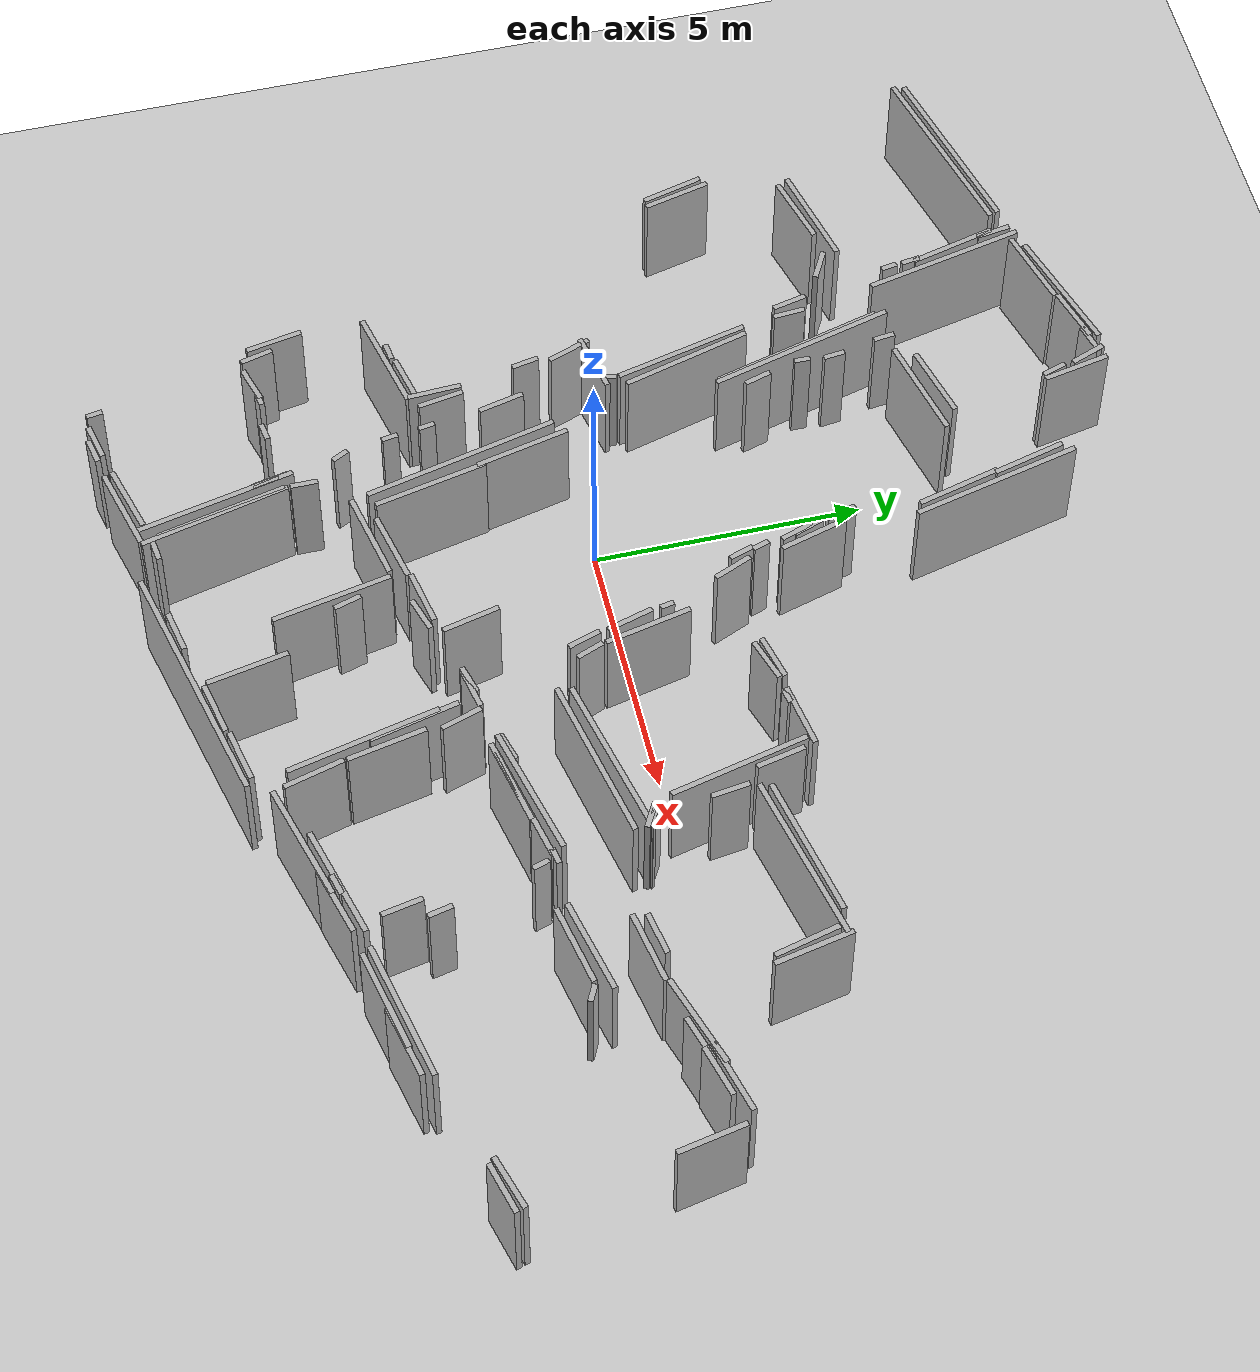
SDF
<?xml version="1.0" ?>
<sdf version="1.6">
  <world name="slam_world">
    <physics name="default_physics" default="0" type="ode">
      <max_step_size>0.001</max_step_size>
      <real_time_factor>1</real_time_factor>
      <real_time_update_rate>1000</real_time_update_rate>
    </physics>
    <gravity>0 0 -9.8</gravity>
    <scene>
      <ambient>0.4 0.4 0.4 1</ambient>
      <background>0.7 0.7 0.7 1</background>
      <shadows>true</shadows>
    </scene>
    <light name="sun" type="directional">
      <cast_shadows>1</cast_shadows>
      <pose>0 0 10 0 0 0</pose>
      <diffuse>0.8 0.8 0.8 1</diffuse>
      <specular>0.2 0.2 0.2 1</specular>
      <attenuation>1 0.0 0.0</attenuation>
      <direction>-0.5 0.1 -0.9</direction>
    </light>
    <model name="ground_plane">
      <static>true</static>
      <link name="link">
        <collision name="collision">
          <geometry>
            <plane>
              <normal>0 0 1</normal>
              <size>100 100</size>
            </plane>
          </geometry>
        </collision>
        <visual name="visual">
          <geometry>
            <plane>
              <normal>0 0 1</normal>
              <size>100 100</size>
            </plane>
          </geometry>
          <material>
            <ambient>0.8 0.8 0.8 1</ambient>
            <diffuse>0.8 0.8 0.8 1</diffuse>
            <specular>0.8 0.8 0.8 1</specular>
          </material>
        </visual>
      </link>
    </model>
    <model name="wall_0">
      <static>true</static>
      <pose>0.2850000000000019 -3.74 1.0 0 0 0.21866894587394195</pose>
      <link name="link">
        <collision name="collision">
          <geometry>
            <box>
              <size>1.3829316685939332 0.1 2.0</size>
            </box>
          </geometry>
        </collision>
        <visual name="visual">
          <geometry>
            <box>
              <size>1.3829316685939332 0.1 2.0</size>
            </box>
          </geometry>
          <material>
            <ambient>0.5 0.5 0.5 1</ambient>
            <diffuse>0.7 0.7 0.7 1</diffuse>
            <specular>0.1 0.1 0.1 1</specular>
          </material>
        </visual>
      </link>
    </model>
    <model name="wall_1">
      <static>true</static>
      <pose>4.885000000000002 -2.665 1.0 0 0 0.2662520491509254</pose>
      <link name="link">
        <collision name="collision">
          <geometry>
            <box>
              <size>0.570087712549569 0.1 2.0</size>
            </box>
          </geometry>
        </collision>
        <visual name="visual">
          <geometry>
            <box>
              <size>0.570087712549569 0.1 2.0</size>
            </box>
          </geometry>
          <material>
            <ambient>0.5 0.5 0.5 1</ambient>
            <diffuse>0.7 0.7 0.7 1</diffuse>
            <specular>0.1 0.1 0.1 1</specular>
          </material>
        </visual>
      </link>
    </model>
    <model name="wall_2">
      <static>true</static>
      <pose>-6.464999999999999 8.485 1.0 0 0 0.24156570709532596</pose>
      <link name="link">
        <collision name="collision">
          <geometry>
            <box>
              <size>3.553167600887974 0.1 2.0</size>
            </box>
          </geometry>
        </collision>
        <visual name="visual">
          <geometry>
            <box>
              <size>3.553167600887974 0.1 2.0</size>
            </box>
          </geometry>
          <material>
            <ambient>0.5 0.5 0.5 1</ambient>
            <diffuse>0.7 0.7 0.7 1</diffuse>
            <specular>0.1 0.1 0.1 1</specular>
          </material>
        </visual>
      </link>
    </model>
    <model name="wall_3">
      <static>true</static>
      <pose>-0.03999999999999915 -4.065 1.0 0 0 0.20304521725346514</pose>
      <link name="link">
        <collision name="collision">
          <geometry>
            <box>
              <size>1.7356554957709784 0.1 2.0</size>
            </box>
          </geometry>
        </collision>
        <visual name="visual">
          <geometry>
            <box>
              <size>1.7356554957709784 0.1 2.0</size>
            </box>
          </geometry>
          <material>
            <ambient>0.5 0.5 0.5 1</ambient>
            <diffuse>0.7 0.7 0.7 1</diffuse>
            <specular>0.1 0.1 0.1 1</specular>
          </material>
        </visual>
      </link>
    </model>
    <model name="wall_4">
      <static>true</static>
      <pose>-0.589999999999999 -7.815 1.0 0 0 0.12435499454676144</pose>
      <link name="link">
        <collision name="collision">
          <geometry>
            <box>
              <size>0.40311288741492746 0.1 2.0</size>
            </box>
          </geometry>
        </collision>
        <visual name="visual">
          <geometry>
            <box>
              <size>0.40311288741492746 0.1 2.0</size>
            </box>
          </geometry>
          <material>
            <ambient>0.5 0.5 0.5 1</ambient>
            <diffuse>0.7 0.7 0.7 1</diffuse>
            <specular>0.1 0.1 0.1 1</specular>
          </material>
        </visual>
      </link>
    </model>
    <model name="wall_5">
      <static>true</static>
      <pose>13.035000000000004 -4.565 1.0 0 0 0.25732371497108864</pose>
      <link name="link">
        <collision name="collision">
          <geometry>
            <box>
              <size>0.982344135219425 0.1 2.0</size>
            </box>
          </geometry>
        </collision>
        <visual name="visual">
          <geometry>
            <box>
              <size>0.982344135219425 0.1 2.0</size>
            </box>
          </geometry>
          <material>
            <ambient>0.5 0.5 0.5 1</ambient>
            <diffuse>0.7 0.7 0.7 1</diffuse>
            <specular>0.1 0.1 0.1 1</specular>
          </material>
        </visual>
      </link>
    </model>
    <model name="wall_6">
      <static>true</static>
      <pose>-3.514999999999999 4.535 1.0 0 0 -1.3439974787410107</pose>
      <link name="link">
        <collision name="collision">
          <geometry>
            <box>
              <size>0.6670832032063168 0.1 2.0</size>
            </box>
          </geometry>
        </collision>
        <visual name="visual">
          <geometry>
            <box>
              <size>0.6670832032063168 0.1 2.0</size>
            </box>
          </geometry>
          <material>
            <ambient>0.5 0.5 0.5 1</ambient>
            <diffuse>0.7 0.7 0.7 1</diffuse>
            <specular>0.1 0.1 0.1 1</specular>
          </material>
        </visual>
      </link>
    </model>
    <model name="wall_7">
      <static>true</static>
      <pose>5.960000000000001 -6.44 1.0 0 0 0.2662520491509254</pose>
      <link name="link">
        <collision name="collision">
          <geometry>
            <box>
              <size>2.280350850198276 0.1 2.0</size>
            </box>
          </geometry>
        </collision>
        <visual name="visual">
          <geometry>
            <box>
              <size>2.280350850198276 0.1 2.0</size>
            </box>
          </geometry>
          <material>
            <ambient>0.5 0.5 0.5 1</ambient>
            <diffuse>0.7 0.7 0.7 1</diffuse>
            <specular>0.1 0.1 0.1 1</specular>
          </material>
        </visual>
      </link>
    </model>
    <model name="wall_8">
      <static>true</static>
      <pose>-1.339999999999999 -1.0150000000000006 1.0 0 0 -1.346085158380254</pose>
      <link name="link">
        <collision name="collision">
          <geometry>
            <box>
              <size>1.795132307101624 0.1 2.0</size>
            </box>
          </geometry>
        </collision>
        <visual name="visual">
          <geometry>
            <box>
              <size>1.795132307101624 0.1 2.0</size>
            </box>
          </geometry>
          <material>
            <ambient>0.5 0.5 0.5 1</ambient>
            <diffuse>0.7 0.7 0.7 1</diffuse>
            <specular>0.1 0.1 0.1 1</specular>
          </material>
        </visual>
      </link>
    </model>
    <model name="wall_9">
      <static>true</static>
      <pose>-2.639999999999999 9.510000000000002 1.0 0 0 0.28379410920832787</pose>
      <link name="link">
        <collision name="collision">
          <geometry>
            <box>
              <size>2.5 0.1 2.0</size>
            </box>
          </geometry>
        </collision>
        <visual name="visual">
          <geometry>
            <box>
              <size>2.5 0.1 2.0</size>
            </box>
          </geometry>
          <material>
            <ambient>0.5 0.5 0.5 1</ambient>
            <diffuse>0.7 0.7 0.7 1</diffuse>
            <specular>0.1 0.1 0.1 1</specular>
          </material>
        </visual>
      </link>
    </model>
    <model name="wall_10">
      <static>true</static>
      <pose>4.185000000000002 -5.040000000000001 1.0 0 0 -1.3426936985149538</pose>
      <link name="link">
        <collision name="collision">
          <geometry>
            <box>
              <size>2.874456470360962 0.1 2.0</size>
            </box>
          </geometry>
        </collision>
        <visual name="visual">
          <geometry>
            <box>
              <size>2.874456470360962 0.1 2.0</size>
            </box>
          </geometry>
          <material>
            <ambient>0.5 0.5 0.5 1</ambient>
            <diffuse>0.7 0.7 0.7 1</diffuse>
            <specular>0.1 0.1 0.1 1</specular>
          </material>
        </visual>
      </link>
    </model>
    <model name="wall_11">
      <static>true</static>
      <pose>9.510000000000002 -5.465 1.0 0 0 0.20846521837998772</pose>
      <link name="link">
        <collision name="collision">
          <geometry>
            <box>
              <size>2.6575364531836625 0.1 2.0</size>
            </box>
          </geometry>
        </collision>
        <visual name="visual">
          <geometry>
            <box>
              <size>2.6575364531836625 0.1 2.0</size>
            </box>
          </geometry>
          <material>
            <ambient>0.5 0.5 0.5 1</ambient>
            <diffuse>0.7 0.7 0.7 1</diffuse>
            <specular>0.1 0.1 0.1 1</specular>
          </material>
        </visual>
      </link>
    </model>
    <model name="wall_12">
      <static>true</static>
      <pose>-2.214999999999999 -2.59 1.0 0 0 -1.4056476493802699</pose>
      <link name="link">
        <collision name="collision">
          <geometry>
            <box>
              <size>0.304138126514911 0.1 2.0</size>
            </box>
          </geometry>
        </collision>
        <visual name="visual">
          <geometry>
            <box>
              <size>0.304138126514911 0.1 2.0</size>
            </box>
          </geometry>
          <material>
            <ambient>0.5 0.5 0.5 1</ambient>
            <diffuse>0.7 0.7 0.7 1</diffuse>
            <specular>0.1 0.1 0.1 1</specular>
          </material>
        </visual>
      </link>
    </model>
    <model name="wall_13">
      <static>true</static>
      <pose>-2.1149999999999984 -3.29 1.0 0 0 -1.4056476493802699</pose>
      <link name="link">
        <collision name="collision">
          <geometry>
            <box>
              <size>0.304138126514911 0.1 2.0</size>
            </box>
          </geometry>
        </collision>
        <visual name="visual">
          <geometry>
            <box>
              <size>0.304138126514911 0.1 2.0</size>
            </box>
          </geometry>
          <material>
            <ambient>0.5 0.5 0.5 1</ambient>
            <diffuse>0.7 0.7 0.7 1</diffuse>
            <specular>0.1 0.1 0.1 1</specular>
          </material>
        </visual>
      </link>
    </model>
    <model name="wall_14">
      <static>true</static>
      <pose>-3.8649999999999993 7.609999999999999 1.0 0 0 -1.3574276846430886</pose>
      <link name="link">
        <collision name="collision">
          <geometry>
            <box>
              <size>3.0696090956341657 0.1 2.0</size>
            </box>
          </geometry>
        </collision>
        <visual name="visual">
          <geometry>
            <box>
              <size>3.0696090956341657 0.1 2.0</size>
            </box>
          </geometry>
          <material>
            <ambient>0.5 0.5 0.5 1</ambient>
            <diffuse>0.7 0.7 0.7 1</diffuse>
            <specular>0.1 0.1 0.1 1</specular>
          </material>
        </visual>
      </link>
    </model>
    <model name="wall_15">
      <static>true</static>
      <pose>1.2100000000000009 -7.765000000000001 1.0 0 0 0.18534794999569476</pose>
      <link name="link">
        <collision name="collision">
          <geometry>
            <box>
              <size>0.8139410298049854 0.1 2.0</size>
            </box>
          </geometry>
        </collision>
        <visual name="visual">
          <geometry>
            <box>
              <size>0.8139410298049854 0.1 2.0</size>
            </box>
          </geometry>
          <material>
            <ambient>0.5 0.5 0.5 1</ambient>
            <diffuse>0.7 0.7 0.7 1</diffuse>
            <specular>0.1 0.1 0.1 1</specular>
          </material>
        </visual>
      </link>
    </model>
    <model name="wall_16">
      <static>true</static>
      <pose>0.9850000000000012 7.785 1.0 0 0 -1.317122230656254</pose>
      <link name="link">
        <collision name="collision">
          <geometry>
            <box>
              <size>1.3946325680981353 0.1 2.0</size>
            </box>
          </geometry>
        </collision>
        <visual name="visual">
          <geometry>
            <box>
              <size>1.3946325680981353 0.1 2.0</size>
            </box>
          </geometry>
          <material>
            <ambient>0.5 0.5 0.5 1</ambient>
            <diffuse>0.7 0.7 0.7 1</diffuse>
            <specular>0.1 0.1 0.1 1</specular>
          </material>
        </visual>
      </link>
    </model>
    <model name="wall_17">
      <static>true</static>
      <pose>-4.139999999999999 7.859999999999999 1.0 0 0 -1.3258176636680326</pose>
      <link name="link">
        <collision name="collision">
          <geometry>
            <box>
              <size>1.6492422502470643 0.1 2.0</size>
            </box>
          </geometry>
        </collision>
        <visual name="visual">
          <geometry>
            <box>
              <size>1.6492422502470643 0.1 2.0</size>
            </box>
          </geometry>
          <material>
            <ambient>0.5 0.5 0.5 1</ambient>
            <diffuse>0.7 0.7 0.7 1</diffuse>
            <specular>0.1 0.1 0.1 1</specular>
          </material>
        </visual>
      </link>
    </model>
    <model name="wall_18">
      <static>true</static>
      <pose>-3.2399999999999984 -8.465 1.0 0 0 0.21109333322274654</pose>
      <link name="link">
        <collision name="collision">
          <geometry>
            <box>
              <size>0.7158910531638177 0.1 2.0</size>
            </box>
          </geometry>
        </collision>
        <visual name="visual">
          <geometry>
            <box>
              <size>0.7158910531638177 0.1 2.0</size>
            </box>
          </geometry>
          <material>
            <ambient>0.5 0.5 0.5 1</ambient>
            <diffuse>0.7 0.7 0.7 1</diffuse>
            <specular>0.1 0.1 0.1 1</specular>
          </material>
        </visual>
      </link>
    </model>
    <model name="wall_19">
      <static>true</static>
      <pose>6.160000000000002 1.0850000000000009 1.0 0 0 -1.3397056595989996</pose>
      <link name="link">
        <collision name="collision">
          <geometry>
            <box>
              <size>2.6196373794859475 0.1 2.0</size>
            </box>
          </geometry>
        </collision>
        <visual name="visual">
          <geometry>
            <box>
              <size>2.6196373794859475 0.1 2.0</size>
            </box>
          </geometry>
          <material>
            <ambient>0.5 0.5 0.5 1</ambient>
            <diffuse>0.7 0.7 0.7 1</diffuse>
            <specular>0.1 0.1 0.1 1</specular>
          </material>
        </visual>
      </link>
    </model>
    <model name="wall_20">
      <static>true</static>
      <pose>-6.464999999999999 8.309999999999999 1.0 0 0 0.24828990930306807</pose>
      <link name="link">
        <collision name="collision">
          <geometry>
            <box>
              <size>3.6623080154459977 0.1 2.0</size>
            </box>
          </geometry>
        </collision>
        <visual name="visual">
          <geometry>
            <box>
              <size>3.6623080154459977 0.1 2.0</size>
            </box>
          </geometry>
          <material>
            <ambient>0.5 0.5 0.5 1</ambient>
            <diffuse>0.7 0.7 0.7 1</diffuse>
            <specular>0.1 0.1 0.1 1</specular>
          </material>
        </visual>
      </link>
    </model>
    <model name="wall_21">
      <static>true</static>
      <pose>-2.664999999999999 2.3599999999999994 1.0 0 0 -1.306307944245664</pose>
      <link name="link">
        <collision name="collision">
          <geometry>
            <box>
              <size>2.4864633518312713 0.1 2.0</size>
            </box>
          </geometry>
        </collision>
        <visual name="visual">
          <geometry>
            <box>
              <size>2.4864633518312713 0.1 2.0</size>
            </box>
          </geometry>
          <material>
            <ambient>0.5 0.5 0.5 1</ambient>
            <diffuse>0.7 0.7 0.7 1</diffuse>
            <specular>0.1 0.1 0.1 1</specular>
          </material>
        </visual>
      </link>
    </model>
    <model name="wall_22">
      <static>true</static>
      <pose>-3.389999999999999 -2.74 1.0 0 0 0.21866894587394195</pose>
      <link name="link">
        <collision name="collision">
          <geometry>
            <box>
              <size>0.9219544457292888 0.1 2.0</size>
            </box>
          </geometry>
        </collision>
        <visual name="visual">
          <geometry>
            <box>
              <size>0.9219544457292888 0.1 2.0</size>
            </box>
          </geometry>
          <material>
            <ambient>0.5 0.5 0.5 1</ambient>
            <diffuse>0.7 0.7 0.7 1</diffuse>
            <specular>0.1 0.1 0.1 1</specular>
          </material>
        </visual>
      </link>
    </model>
    <model name="wall_23">
      <static>true</static>
      <pose>11.135000000000002 -0.8650000000000002 1.0 0 0 0.2860514417173182</pose>
      <link name="link">
        <collision name="collision">
          <geometry>
            <box>
              <size>0.8860022573334675 0.1 2.0</size>
            </box>
          </geometry>
        </collision>
        <visual name="visual">
          <geometry>
            <box>
              <size>0.8860022573334675 0.1 2.0</size>
            </box>
          </geometry>
          <material>
            <ambient>0.5 0.5 0.5 1</ambient>
            <diffuse>0.7 0.7 0.7 1</diffuse>
            <specular>0.1 0.1 0.1 1</specular>
          </material>
        </visual>
      </link>
    </model>
    <model name="wall_24">
      <static>true</static>
      <pose>-3.889999999999999 -3.0150000000000006 1.0 0 0 0.2213144423477913</pose>
      <link name="link">
        <collision name="collision">
          <geometry>
            <box>
              <size>2.0500000000000003 0.1 2.0</size>
            </box>
          </geometry>
        </collision>
        <visual name="visual">
          <geometry>
            <box>
              <size>2.0500000000000003 0.1 2.0</size>
            </box>
          </geometry>
          <material>
            <ambient>0.5 0.5 0.5 1</ambient>
            <diffuse>0.7 0.7 0.7 1</diffuse>
            <specular>0.1 0.1 0.1 1</specular>
          </material>
        </visual>
      </link>
    </model>
    <model name="wall_25">
      <static>true</static>
      <pose>10.085 -5.540000000000001 1.0 0 0 0.21866894587394195</pose>
      <link name="link">
        <collision name="collision">
          <geometry>
            <box>
              <size>1.3829316685939332 0.1 2.0</size>
            </box>
          </geometry>
        </collision>
        <visual name="visual">
          <geometry>
            <box>
              <size>1.3829316685939332 0.1 2.0</size>
            </box>
          </geometry>
          <material>
            <ambient>0.5 0.5 0.5 1</ambient>
            <diffuse>0.7 0.7 0.7 1</diffuse>
            <specular>0.1 0.1 0.1 1</specular>
          </material>
        </visual>
      </link>
    </model>
    <model name="wall_26">
      <static>true</static>
      <pose>11.935000000000002 -0.5150000000000006 1.0 0 0 0.2536740961386427</pose>
      <link name="link">
        <collision name="collision">
          <geometry>
            <box>
              <size>1.3946325680981353 0.1 2.0</size>
            </box>
          </geometry>
        </collision>
        <visual name="visual">
          <geometry>
            <box>
              <size>1.3946325680981353 0.1 2.0</size>
            </box>
          </geometry>
          <material>
            <ambient>0.5 0.5 0.5 1</ambient>
            <diffuse>0.7 0.7 0.7 1</diffuse>
            <specular>0.1 0.1 0.1 1</specular>
          </material>
        </visual>
      </link>
    </model>
    <model name="wall_27">
      <static>true</static>
      <pose>1.3100000000000023 6.385 1.0 0 0 -1.3182420510168371</pose>
      <link name="link">
        <collision name="collision">
          <geometry>
            <box>
              <size>1.6007810593582121 0.1 2.0</size>
            </box>
          </geometry>
        </collision>
        <visual name="visual">
          <geometry>
            <box>
              <size>1.6007810593582121 0.1 2.0</size>
            </box>
          </geometry>
          <material>
            <ambient>0.5 0.5 0.5 1</ambient>
            <diffuse>0.7 0.7 0.7 1</diffuse>
            <specular>0.1 0.1 0.1 1</specular>
          </material>
        </visual>
      </link>
    </model>
    <model name="wall_28">
      <static>true</static>
      <pose>9.060000000000002 -1.0650000000000004 1.0 0 0 0.18534794999569476</pose>
      <link name="link">
        <collision name="collision">
          <geometry>
            <box>
              <size>0.8139410298049854 0.1 2.0</size>
            </box>
          </geometry>
        </collision>
        <visual name="visual">
          <geometry>
            <box>
              <size>0.8139410298049854 0.1 2.0</size>
            </box>
          </geometry>
          <material>
            <ambient>0.5 0.5 0.5 1</ambient>
            <diffuse>0.7 0.7 0.7 1</diffuse>
            <specular>0.1 0.1 0.1 1</specular>
          </material>
        </visual>
      </link>
    </model>
    <model name="wall_29">
      <static>true</static>
      <pose>3.0100000000000016 -0.8900000000000006 1.0 0 0 -1.2490457723982544</pose>
      <link name="link">
        <collision name="collision">
          <geometry>
            <box>
              <size>0.632455532033676 0.1 2.0</size>
            </box>
          </geometry>
        </collision>
        <visual name="visual">
          <geometry>
            <box>
              <size>0.632455532033676 0.1 2.0</size>
            </box>
          </geometry>
          <material>
            <ambient>0.5 0.5 0.5 1</ambient>
            <diffuse>0.7 0.7 0.7 1</diffuse>
            <specular>0.1 0.1 0.1 1</specular>
          </material>
        </visual>
      </link>
    </model>
    <model name="wall_30">
      <static>true</static>
      <pose>7.210000000000001 -2.365 1.0 0 0 0.16514867741462683</pose>
      <link name="link">
        <collision name="collision">
          <geometry>
            <box>
              <size>0.304138126514911 0.1 2.0</size>
            </box>
          </geometry>
        </collision>
        <visual name="visual">
          <geometry>
            <box>
              <size>0.304138126514911 0.1 2.0</size>
            </box>
          </geometry>
          <material>
            <ambient>0.5 0.5 0.5 1</ambient>
            <diffuse>0.7 0.7 0.7 1</diffuse>
            <specular>0.1 0.1 0.1 1</specular>
          </material>
        </visual>
      </link>
    </model>
    <model name="wall_31">
      <static>true</static>
      <pose>1.3350000000000009 7.085000000000001 1.0 0 0 -1.3370531459259951</pose>
      <link name="link">
        <collision name="collision">
          <geometry>
            <box>
              <size>3.2380549717384355 0.1 2.0</size>
            </box>
          </geometry>
        </collision>
        <visual name="visual">
          <geometry>
            <box>
              <size>3.2380549717384355 0.1 2.0</size>
            </box>
          </geometry>
          <material>
            <ambient>0.5 0.5 0.5 1</ambient>
            <diffuse>0.7 0.7 0.7 1</diffuse>
            <specular>0.1 0.1 0.1 1</specular>
          </material>
        </visual>
      </link>
    </model>
    <model name="wall_32">
      <static>true</static>
      <pose>-2.839999999999999 2.3100000000000005 1.0 0 0 -1.3352513460740332</pose>
      <link name="link">
        <collision name="collision">
          <geometry>
            <box>
              <size>2.5709920264364885 0.1 2.0</size>
            </box>
          </geometry>
        </collision>
        <visual name="visual">
          <geometry>
            <box>
              <size>2.5709920264364885 0.1 2.0</size>
            </box>
          </geometry>
          <material>
            <ambient>0.5 0.5 0.5 1</ambient>
            <diffuse>0.7 0.7 0.7 1</diffuse>
            <specular>0.1 0.1 0.1 1</specular>
          </material>
        </visual>
      </link>
    </model>
    <model name="wall_33">
      <static>true</static>
      <pose>2.335000000000001 -7.665000000000001 1.0 0 0 0.22208190190548016</pose>
      <link name="link">
        <collision name="collision">
          <geometry>
            <box>
              <size>4.767074574621211 0.1 2.0</size>
            </box>
          </geometry>
        </collision>
        <visual name="visual">
          <geometry>
            <box>
              <size>4.767074574621211 0.1 2.0</size>
            </box>
          </geometry>
          <material>
            <ambient>0.5 0.5 0.5 1</ambient>
            <diffuse>0.7 0.7 0.7 1</diffuse>
            <specular>0.1 0.1 0.1 1</specular>
          </material>
        </visual>
      </link>
    </model>
    <model name="wall_34">
      <static>true</static>
      <pose>6.860000000000001 -6.015000000000001 1.0 0 0 0.25615138256560344</pose>
      <link name="link">
        <collision name="collision">
          <geometry>
            <box>
              <size>2.170829334609241 0.1 2.0</size>
            </box>
          </geometry>
        </collision>
        <visual name="visual">
          <geometry>
            <box>
              <size>2.170829334609241 0.1 2.0</size>
            </box>
          </geometry>
          <material>
            <ambient>0.5 0.5 0.5 1</ambient>
            <diffuse>0.7 0.7 0.7 1</diffuse>
            <specular>0.1 0.1 0.1 1</specular>
          </material>
        </visual>
      </link>
    </model>
    <model name="wall_35">
      <static>true</static>
      <pose>-1.4149999999999991 -6.615 1.0 0 0 -1.3539227111284884</pose>
      <link name="link">
        <collision name="collision">
          <geometry>
            <box>
              <size>3.020761493398643 0.1 2.0</size>
            </box>
          </geometry>
        </collision>
        <visual name="visual">
          <geometry>
            <box>
              <size>3.020761493398643 0.1 2.0</size>
            </box>
          </geometry>
          <material>
            <ambient>0.5 0.5 0.5 1</ambient>
            <diffuse>0.7 0.7 0.7 1</diffuse>
            <specular>0.1 0.1 0.1 1</specular>
          </material>
        </visual>
      </link>
    </model>
    <model name="wall_36">
      <static>true</static>
      <pose>-3.039999999999999 -8.540000000000001 1.0 0 0 0.19739555984988075</pose>
      <link name="link">
        <collision name="collision">
          <geometry>
            <box>
              <size>0.5099019513592785 0.1 2.0</size>
            </box>
          </geometry>
        </collision>
        <visual name="visual">
          <geometry>
            <box>
              <size>0.5099019513592785 0.1 2.0</size>
            </box>
          </geometry>
          <material>
            <ambient>0.5 0.5 0.5 1</ambient>
            <diffuse>0.7 0.7 0.7 1</diffuse>
            <specular>0.1 0.1 0.1 1</specular>
          </material>
        </visual>
      </link>
    </model>
    <model name="wall_37">
      <static>true</static>
      <pose>5.585000000000001 -2.7650000000000006 1.0 0 0 0.20902294280626463</pose>
      <link name="link">
        <collision name="collision">
          <geometry>
            <box>
              <size>1.6867127793433 0.1 2.0</size>
            </box>
          </geometry>
        </collision>
        <visual name="visual">
          <geometry>
            <box>
              <size>1.6867127793433 0.1 2.0</size>
            </box>
          </geometry>
          <material>
            <ambient>0.5 0.5 0.5 1</ambient>
            <diffuse>0.7 0.7 0.7 1</diffuse>
            <specular>0.1 0.1 0.1 1</specular>
          </material>
        </visual>
      </link>
    </model>
    <model name="wall_38">
      <static>true</static>
      <pose>-1.0649999999999986 9.535 1.0 0 0 -1.2036224929766774</pose>
      <link name="link">
        <collision name="collision">
          <geometry>
            <box>
              <size>0.696419413859206 0.1 2.0</size>
            </box>
          </geometry>
        </collision>
        <visual name="visual">
          <geometry>
            <box>
              <size>0.696419413859206 0.1 2.0</size>
            </box>
          </geometry>
          <material>
            <ambient>0.5 0.5 0.5 1</ambient>
            <diffuse>0.7 0.7 0.7 1</diffuse>
            <specular>0.1 0.1 0.1 1</specular>
          </material>
        </visual>
      </link>
    </model>
    <model name="wall_39">
      <static>true</static>
      <pose>5.460000000000001 -1.2650000000000006 1.0 0 0 0.20668321848424925</pose>
      <link name="link">
        <collision name="collision">
          <geometry>
            <box>
              <size>3.167412192942371 0.1 2.0</size>
            </box>
          </geometry>
        </collision>
        <visual name="visual">
          <geometry>
            <box>
              <size>3.167412192942371 0.1 2.0</size>
            </box>
          </geometry>
          <material>
            <ambient>0.5 0.5 0.5 1</ambient>
            <diffuse>0.7 0.7 0.7 1</diffuse>
            <specular>0.1 0.1 0.1 1</specular>
          </material>
        </visual>
      </link>
    </model>
    <model name="wall_40">
      <static>true</static>
      <pose>4.135000000000002 2.210000000000001 1.0 0 0 0.23109066719589708</pose>
      <link name="link">
        <collision name="collision">
          <geometry>
            <box>
              <size>0.873212459828649 0.1 2.0</size>
            </box>
          </geometry>
        </collision>
        <visual name="visual">
          <geometry>
            <box>
              <size>0.873212459828649 0.1 2.0</size>
            </box>
          </geometry>
          <material>
            <ambient>0.5 0.5 0.5 1</ambient>
            <diffuse>0.7 0.7 0.7 1</diffuse>
            <specular>0.1 0.1 0.1 1</specular>
          </material>
        </visual>
      </link>
    </model>
    <model name="wall_41">
      <static>true</static>
      <pose>3.3850000000000016 -3.0150000000000006 1.0 0 0 0.2662520491509254</pose>
      <link name="link">
        <collision name="collision">
          <geometry>
            <box>
              <size>0.570087712549569 0.1 2.0</size>
            </box>
          </geometry>
        </collision>
        <visual name="visual">
          <geometry>
            <box>
              <size>0.570087712549569 0.1 2.0</size>
            </box>
          </geometry>
          <material>
            <ambient>0.5 0.5 0.5 1</ambient>
            <diffuse>0.7 0.7 0.7 1</diffuse>
            <specular>0.1 0.1 0.1 1</specular>
          </material>
        </visual>
      </link>
    </model>
    <model name="wall_42">
      <static>true</static>
      <pose>5.410000000000002 2.3599999999999994 1.0 0 0 0.16514867741462683</pose>
      <link name="link">
        <collision name="collision">
          <geometry>
            <box>
              <size>1.216552506059644 0.1 2.0</size>
            </box>
          </geometry>
        </collision>
        <visual name="visual">
          <geometry>
            <box>
              <size>1.216552506059644 0.1 2.0</size>
            </box>
          </geometry>
          <material>
            <ambient>0.5 0.5 0.5 1</ambient>
            <diffuse>0.7 0.7 0.7 1</diffuse>
            <specular>0.1 0.1 0.1 1</specular>
          </material>
        </visual>
      </link>
    </model>
    <model name="wall_43">
      <static>true</static>
      <pose>4.660000000000002 -5.99 1.0 0 0 -1.3045442776439713</pose>
      <link name="link">
        <collision name="collision">
          <geometry>
            <box>
              <size>1.140175425099138 0.1 2.0</size>
            </box>
          </geometry>
        </collision>
        <visual name="visual">
          <geometry>
            <box>
              <size>1.140175425099138 0.1 2.0</size>
            </box>
          </geometry>
          <material>
            <ambient>0.5 0.5 0.5 1</ambient>
            <diffuse>0.7 0.7 0.7 1</diffuse>
            <specular>0.1 0.1 0.1 1</specular>
          </material>
        </visual>
      </link>
    </model>
    <model name="wall_44">
      <static>true</static>
      <pose>7.310000000000002 -2.6400000000000006 1.0 0 0 -1.2490457723982544</pose>
      <link name="link">
        <collision name="collision">
          <geometry>
            <box>
              <size>0.316227766016838 0.1 2.0</size>
            </box>
          </geometry>
        </collision>
        <visual name="visual">
          <geometry>
            <box>
              <size>0.316227766016838 0.1 2.0</size>
            </box>
          </geometry>
          <material>
            <ambient>0.5 0.5 0.5 1</ambient>
            <diffuse>0.7 0.7 0.7 1</diffuse>
            <specular>0.1 0.1 0.1 1</specular>
          </material>
        </visual>
      </link>
    </model>
    <model name="wall_45">
      <static>true</static>
      <pose>10.810000000000002 -0.8150000000000004 1.0 0 0 0.3129012278803845</pose>
      <link name="link">
        <collision name="collision">
          <geometry>
            <box>
              <size>1.7867568385205637 0.1 2.0</size>
            </box>
          </geometry>
        </collision>
        <visual name="visual">
          <geometry>
            <box>
              <size>1.7867568385205637 0.1 2.0</size>
            </box>
          </geometry>
          <material>
            <ambient>0.5 0.5 0.5 1</ambient>
            <diffuse>0.7 0.7 0.7 1</diffuse>
            <specular>0.1 0.1 0.1 1</specular>
          </material>
        </visual>
      </link>
    </model>
    <model name="wall_46">
      <static>true</static>
      <pose>-1.089999999999999 6.635 1.0 0 0 0.24497866312686414</pose>
      <link name="link">
        <collision name="collision">
          <geometry>
            <box>
              <size>1.4430869689661812 0.1 2.0</size>
            </box>
          </geometry>
        </collision>
        <visual name="visual">
          <geometry>
            <box>
              <size>1.4430869689661812 0.1 2.0</size>
            </box>
          </geometry>
          <material>
            <ambient>0.5 0.5 0.5 1</ambient>
            <diffuse>0.7 0.7 0.7 1</diffuse>
            <specular>0.1 0.1 0.1 1</specular>
          </material>
        </visual>
      </link>
    </model>
    <model name="wall_47">
      <static>true</static>
      <pose>-1.3649999999999984 -2.1400000000000006 1.0 0 0 -1.338931665945508</pose>
      <link name="link">
        <collision name="collision">
          <geometry>
            <box>
              <size>3.6989863476363363 0.1 2.0</size>
            </box>
          </geometry>
        </collision>
        <visual name="visual">
          <geometry>
            <box>
              <size>3.6989863476363363 0.1 2.0</size>
            </box>
          </geometry>
          <material>
            <ambient>0.5 0.5 0.5 1</ambient>
            <diffuse>0.7 0.7 0.7 1</diffuse>
            <specular>0.1 0.1 0.1 1</specular>
          </material>
        </visual>
      </link>
    </model>
    <model name="wall_48">
      <static>true</static>
      <pose>11.785000000000004 -0.7149999999999999 1.0 0 0 0.25732371497108864</pose>
      <link name="link">
        <collision name="collision">
          <geometry>
            <box>
              <size>0.982344135219425 0.1 2.0</size>
            </box>
          </geometry>
        </collision>
        <visual name="visual">
          <geometry>
            <box>
              <size>0.982344135219425 0.1 2.0</size>
            </box>
          </geometry>
          <material>
            <ambient>0.5 0.5 0.5 1</ambient>
            <diffuse>0.7 0.7 0.7 1</diffuse>
            <specular>0.1 0.1 0.1 1</specular>
          </material>
        </visual>
      </link>
    </model>
    <model name="wall_49">
      <static>true</static>
      <pose>5.835000000000001 -2.49 1.0 0 0 0.2401710078601731</pose>
      <link name="link">
        <collision name="collision">
          <geometry>
            <box>
              <size>2.522399651125888 0.1 2.0</size>
            </box>
          </geometry>
        </collision>
        <visual name="visual">
          <geometry>
            <box>
              <size>2.522399651125888 0.1 2.0</size>
            </box>
          </geometry>
          <material>
            <ambient>0.5 0.5 0.5 1</ambient>
            <diffuse>0.7 0.7 0.7 1</diffuse>
            <specular>0.1 0.1 0.1 1</specular>
          </material>
        </visual>
      </link>
    </model>
    <model name="wall_50">
      <static>true</static>
      <pose>-1.1649999999999991 -6.540000000000001 1.0 0 0 -1.3455195475808412</pose>
      <link name="link">
        <collision name="collision">
          <geometry>
            <box>
              <size>2.4622144504490264 0.1 2.0</size>
            </box>
          </geometry>
        </collision>
        <visual name="visual">
          <geometry>
            <box>
              <size>2.4622144504490264 0.1 2.0</size>
            </box>
          </geometry>
          <material>
            <ambient>0.5 0.5 0.5 1</ambient>
            <diffuse>0.7 0.7 0.7 1</diffuse>
            <specular>0.1 0.1 0.1 1</specular>
          </material>
        </visual>
      </link>
    </model>
    <model name="wall_51">
      <static>true</static>
      <pose>7.810000000000002 -4.465000000000001 1.0 0 0 -1.3521273809209546</pose>
      <link name="link">
        <collision name="collision">
          <geometry>
            <box>
              <size>0.4609772228646444 0.1 2.0</size>
            </box>
          </geometry>
        </collision>
        <visual name="visual">
          <geometry>
            <box>
              <size>0.4609772228646444 0.1 2.0</size>
            </box>
          </geometry>
          <material>
            <ambient>0.5 0.5 0.5 1</ambient>
            <diffuse>0.7 0.7 0.7 1</diffuse>
            <specular>0.1 0.1 0.1 1</specular>
          </material>
        </visual>
      </link>
    </model>
    <model name="wall_52">
      <static>true</static>
      <pose>7.985000000000003 1.7850000000000001 1.0 0 0 0.20464180982977792</pose>
      <link name="link">
        <collision name="collision">
          <geometry>
            <box>
              <size>2.7064737205448717 0.1 2.0</size>
            </box>
          </geometry>
        </collision>
        <visual name="visual">
          <geometry>
            <box>
              <size>2.7064737205448717 0.1 2.0</size>
            </box>
          </geometry>
          <material>
            <ambient>0.5 0.5 0.5 1</ambient>
            <diffuse>0.7 0.7 0.7 1</diffuse>
            <specular>0.1 0.1 0.1 1</specular>
          </material>
        </visual>
      </link>
    </model>
    <model name="wall_53">
      <static>true</static>
      <pose>9.035 -2.1900000000000004 1.0 0 0 0.2247111684146427</pose>
      <link name="link">
        <collision name="collision">
          <geometry>
            <box>
              <size>1.795132307101624 0.1 2.0</size>
            </box>
          </geometry>
        </collision>
        <visual name="visual">
          <geometry>
            <box>
              <size>1.795132307101624 0.1 2.0</size>
            </box>
          </geometry>
          <material>
            <ambient>0.5 0.5 0.5 1</ambient>
            <diffuse>0.7 0.7 0.7 1</diffuse>
            <specular>0.1 0.1 0.1 1</specular>
          </material>
        </visual>
      </link>
    </model>
    <model name="wall_54">
      <static>true</static>
      <pose>-1.839999999999999 -8.115 1.0 0 0 0.2629947316809195</pose>
      <link name="link">
        <collision name="collision">
          <geometry>
            <box>
              <size>1.3462912017836262 0.1 2.0</size>
            </box>
          </geometry>
        </collision>
        <visual name="visual">
          <geometry>
            <box>
              <size>1.3462912017836262 0.1 2.0</size>
            </box>
          </geometry>
          <material>
            <ambient>0.5 0.5 0.5 1</ambient>
            <diffuse>0.7 0.7 0.7 1</diffuse>
            <specular>0.1 0.1 0.1 1</specular>
          </material>
        </visual>
      </link>
    </model>
    <model name="wall_55">
      <static>true</static>
      <pose>-1.0149999999999988 6.335000000000001 1.0 0 0 0.22679884805388587</pose>
      <link name="link">
        <collision name="collision">
          <geometry>
            <box>
              <size>2.00124960961895 0.1 2.0</size>
            </box>
          </geometry>
        </collision>
        <visual name="visual">
          <geometry>
            <box>
              <size>2.00124960961895 0.1 2.0</size>
            </box>
          </geometry>
          <material>
            <ambient>0.5 0.5 0.5 1</ambient>
            <diffuse>0.7 0.7 0.7 1</diffuse>
            <specular>0.1 0.1 0.1 1</specular>
          </material>
        </visual>
      </link>
    </model>
    <model name="wall_56">
      <static>true</static>
      <pose>-2.3149999999999986 6.01 1.0 0 0 -1.446441332248135</pose>
      <link name="link">
        <collision name="collision">
          <geometry>
            <box>
              <size>0.40311288741492746 0.1 2.0</size>
            </box>
          </geometry>
        </collision>
        <visual name="visual">
          <geometry>
            <box>
              <size>0.40311288741492746 0.1 2.0</size>
            </box>
          </geometry>
          <material>
            <ambient>0.5 0.5 0.5 1</ambient>
            <diffuse>0.7 0.7 0.7 1</diffuse>
            <specular>0.1 0.1 0.1 1</specular>
          </material>
        </visual>
      </link>
    </model>
    <model name="wall_57">
      <static>true</static>
      <pose>2.785000000000002 -0.015000000000000568 1.0 0 0 -1.2847448850775784</pose>
      <link name="link">
        <collision name="collision">
          <geometry>
            <box>
              <size>0.8860022573334675 0.1 2.0</size>
            </box>
          </geometry>
        </collision>
        <visual name="visual">
          <geometry>
            <box>
              <size>0.8860022573334675 0.1 2.0</size>
            </box>
          </geometry>
          <material>
            <ambient>0.5 0.5 0.5 1</ambient>
            <diffuse>0.7 0.7 0.7 1</diffuse>
            <specular>0.1 0.1 0.1 1</specular>
          </material>
        </visual>
      </link>
    </model>
    <model name="wall_58">
      <static>true</static>
      <pose>4.010000000000002 -7.140000000000001 1.0 0 0 0.19739555984988075</pose>
      <link name="link">
        <collision name="collision">
          <geometry>
            <box>
              <size>1.019803902718557 0.1 2.0</size>
            </box>
          </geometry>
        </collision>
        <visual name="visual">
          <geometry>
            <box>
              <size>1.019803902718557 0.1 2.0</size>
            </box>
          </geometry>
          <material>
            <ambient>0.5 0.5 0.5 1</ambient>
            <diffuse>0.7 0.7 0.7 1</diffuse>
            <specular>0.1 0.1 0.1 1</specular>
          </material>
        </visual>
      </link>
    </model>
    <model name="wall_59">
      <static>true</static>
      <pose>8.185000000000002 1.6600000000000001 1.0 0 0 0.21866894587394195</pose>
      <link name="link">
        <collision name="collision">
          <geometry>
            <box>
              <size>3.2268405600525107 0.1 2.0</size>
            </box>
          </geometry>
        </collision>
        <visual name="visual">
          <geometry>
            <box>
              <size>3.2268405600525107 0.1 2.0</size>
            </box>
          </geometry>
          <material>
            <ambient>0.5 0.5 0.5 1</ambient>
            <diffuse>0.7 0.7 0.7 1</diffuse>
            <specular>0.1 0.1 0.1 1</specular>
          </material>
        </visual>
      </link>
    </model>
    <model name="wall_60">
      <static>true</static>
      <pose>-2.014999999999999 9.559999999999999 1.0 0 0 0.27829965900511133</pose>
      <link name="link">
        <collision name="collision">
          <geometry>
            <box>
              <size>1.0920164833920778 0.1 2.0</size>
            </box>
          </geometry>
        </collision>
        <visual name="visual">
          <geometry>
            <box>
              <size>1.0920164833920778 0.1 2.0</size>
            </box>
          </geometry>
          <material>
            <ambient>0.5 0.5 0.5 1</ambient>
            <diffuse>0.7 0.7 0.7 1</diffuse>
            <specular>0.1 0.1 0.1 1</specular>
          </material>
        </visual>
      </link>
    </model>
    <model name="wall_61">
      <static>true</static>
      <pose>-1.9149999999999991 3.51 1.0 0 0 -1.2793395323170296</pose>
      <link name="link">
        <collision name="collision">
          <geometry>
            <box>
              <size>0.5220153254455275 0.1 2.0</size>
            </box>
          </geometry>
        </collision>
        <visual name="visual">
          <geometry>
            <box>
              <size>0.5220153254455275 0.1 2.0</size>
            </box>
          </geometry>
          <material>
            <ambient>0.5 0.5 0.5 1</ambient>
            <diffuse>0.7 0.7 0.7 1</diffuse>
            <specular>0.1 0.1 0.1 1</specular>
          </material>
        </visual>
      </link>
    </model>
    <model name="wall_62">
      <static>true</static>
      <pose>1.8350000000000009 2.2349999999999994 1.0 0 0 -1.2490457723982544</pose>
      <link name="link">
        <collision name="collision">
          <geometry>
            <box>
              <size>0.47434164902525694 0.1 2.0</size>
            </box>
          </geometry>
        </collision>
        <visual name="visual">
          <geometry>
            <box>
              <size>0.47434164902525694 0.1 2.0</size>
            </box>
          </geometry>
          <material>
            <ambient>0.5 0.5 0.5 1</ambient>
            <diffuse>0.7 0.7 0.7 1</diffuse>
            <specular>0.1 0.1 0.1 1</specular>
          </material>
        </visual>
      </link>
    </model>
    <model name="wall_63">
      <static>true</static>
      <pose>5.485000000000001 -0.9900000000000002 1.0 0 0 0.225601243836024</pose>
      <link name="link">
        <collision name="collision">
          <geometry>
            <box>
              <size>3.1292970456637703 0.1 2.0</size>
            </box>
          </geometry>
        </collision>
        <visual name="visual">
          <geometry>
            <box>
              <size>3.1292970456637703 0.1 2.0</size>
            </box>
          </geometry>
          <material>
            <ambient>0.5 0.5 0.5 1</ambient>
            <diffuse>0.7 0.7 0.7 1</diffuse>
            <specular>0.1 0.1 0.1 1</specular>
          </material>
        </visual>
      </link>
    </model>
    <model name="wall_64">
      <static>true</static>
      <pose>1.6100000000000012 3.3100000000000005 1.0 0 0 -1.2490457723982544</pose>
      <link name="link">
        <collision name="collision">
          <geometry>
            <box>
              <size>0.632455532033676 0.1 2.0</size>
            </box>
          </geometry>
        </collision>
        <visual name="visual">
          <geometry>
            <box>
              <size>0.632455532033676 0.1 2.0</size>
            </box>
          </geometry>
          <material>
            <ambient>0.5 0.5 0.5 1</ambient>
            <diffuse>0.7 0.7 0.7 1</diffuse>
            <specular>0.1 0.1 0.1 1</specular>
          </material>
        </visual>
      </link>
    </model>
    <model name="wall_65">
      <static>true</static>
      <pose>2.960000000000001 -7.390000000000001 1.0 0 0 0.19739555984988075</pose>
      <link name="link">
        <collision name="collision">
          <geometry>
            <box>
              <size>1.019803902718557 0.1 2.0</size>
            </box>
          </geometry>
        </collision>
        <visual name="visual">
          <geometry>
            <box>
              <size>1.019803902718557 0.1 2.0</size>
            </box>
          </geometry>
          <material>
            <ambient>0.5 0.5 0.5 1</ambient>
            <diffuse>0.7 0.7 0.7 1</diffuse>
            <specular>0.1 0.1 0.1 1</specular>
          </material>
        </visual>
      </link>
    </model>
    <model name="wall_66">
      <static>true</static>
      <pose>9.260000000000002 -5.69 1.0 0 0 0.20749622643520266</pose>
      <link name="link">
        <collision name="collision">
          <geometry>
            <box>
              <size>1.94164878389476 0.1 2.0</size>
            </box>
          </geometry>
        </collision>
        <visual name="visual">
          <geometry>
            <box>
              <size>1.94164878389476 0.1 2.0</size>
            </box>
          </geometry>
          <material>
            <ambient>0.5 0.5 0.5 1</ambient>
            <diffuse>0.7 0.7 0.7 1</diffuse>
            <specular>0.1 0.1 0.1 1</specular>
          </material>
        </visual>
      </link>
    </model>
    <model name="wall_67">
      <static>true</static>
      <pose>-4.064999999999999 -2.915 1.0 0 0 0.14189705460416394</pose>
      <link name="link">
        <collision name="collision">
          <geometry>
            <box>
              <size>0.3535533905932738 0.1 2.0</size>
            </box>
          </geometry>
        </collision>
        <visual name="visual">
          <geometry>
            <box>
              <size>0.3535533905932738 0.1 2.0</size>
            </box>
          </geometry>
          <material>
            <ambient>0.5 0.5 0.5 1</ambient>
            <diffuse>0.7 0.7 0.7 1</diffuse>
            <specular>0.1 0.1 0.1 1</specular>
          </material>
        </visual>
      </link>
    </model>
    <model name="wall_68">
      <static>true</static>
      <pose>3.2600000000000016 -0.8399999999999999 1.0 0 0 -1.1902899496825317</pose>
      <link name="link">
        <collision name="collision">
          <geometry>
            <box>
              <size>0.5385164807134504 0.1 2.0</size>
            </box>
          </geometry>
        </collision>
        <visual name="visual">
          <geometry>
            <box>
              <size>0.5385164807134504 0.1 2.0</size>
            </box>
          </geometry>
          <material>
            <ambient>0.5 0.5 0.5 1</ambient>
            <diffuse>0.7 0.7 0.7 1</diffuse>
            <specular>0.1 0.1 0.1 1</specular>
          </material>
        </visual>
      </link>
    </model>
    <model name="wall_69">
      <static>true</static>
      <pose>-5.464999999999999 5.484999999999999 1.0 0 0 0.22679884805388587</pose>
      <link name="link">
        <collision name="collision">
          <geometry>
            <box>
              <size>2.00124960961895 0.1 2.0</size>
            </box>
          </geometry>
        </collision>
        <visual name="visual">
          <geometry>
            <box>
              <size>2.00124960961895 0.1 2.0</size>
            </box>
          </geometry>
          <material>
            <ambient>0.5 0.5 0.5 1</ambient>
            <diffuse>0.7 0.7 0.7 1</diffuse>
            <specular>0.1 0.1 0.1 1</specular>
          </material>
        </visual>
      </link>
    </model>
    <model name="wall_70">
      <static>true</static>
      <pose>-0.8149999999999986 9.235 1.0 0 0 -1.373400766945016</pose>
      <link name="link">
        <collision name="collision">
          <geometry>
            <box>
              <size>1.2747548783981963 0.1 2.0</size>
            </box>
          </geometry>
        </collision>
        <visual name="visual">
          <geometry>
            <box>
              <size>1.2747548783981963 0.1 2.0</size>
            </box>
          </geometry>
          <material>
            <ambient>0.5 0.5 0.5 1</ambient>
            <diffuse>0.7 0.7 0.7 1</diffuse>
            <specular>0.1 0.1 0.1 1</specular>
          </material>
        </visual>
      </link>
    </model>
    <model name="wall_71">
      <static>true</static>
      <pose>-0.9149999999999991 -2.79 1.0 0 0 -1.35970299357215</pose>
      <link name="link">
        <collision name="collision">
          <geometry>
            <box>
              <size>2.147673159491453 0.1 2.0</size>
            </box>
          </geometry>
        </collision>
        <visual name="visual">
          <geometry>
            <box>
              <size>2.147673159491453 0.1 2.0</size>
            </box>
          </geometry>
          <material>
            <ambient>0.5 0.5 0.5 1</ambient>
            <diffuse>0.7 0.7 0.7 1</diffuse>
            <specular>0.1 0.1 0.1 1</specular>
          </material>
        </visual>
      </link>
    </model>
    <model name="wall_72">
      <static>true</static>
      <pose>3.585000000000001 -3.0150000000000006 1.0 0 0 0.19739555984988075</pose>
      <link name="link">
        <collision name="collision">
          <geometry>
            <box>
              <size>0.7648529270389178 0.1 2.0</size>
            </box>
          </geometry>
        </collision>
        <visual name="visual">
          <geometry>
            <box>
              <size>0.7648529270389178 0.1 2.0</size>
            </box>
          </geometry>
          <material>
            <ambient>0.5 0.5 0.5 1</ambient>
            <diffuse>0.7 0.7 0.7 1</diffuse>
            <specular>0.1 0.1 0.1 1</specular>
          </material>
        </visual>
      </link>
    </model>
    <model name="wall_73">
      <static>true</static>
      <pose>1.7350000000000012 3.585000000000001 1.0 0 0 -1.297787623708186</pose>
      <link name="link">
        <collision name="collision">
          <geometry>
            <box>
              <size>1.2980754985747172 0.1 2.0</size>
            </box>
          </geometry>
        </collision>
        <visual name="visual">
          <geometry>
            <box>
              <size>1.2980754985747172 0.1 2.0</size>
            </box>
          </geometry>
          <material>
            <ambient>0.5 0.5 0.5 1</ambient>
            <diffuse>0.7 0.7 0.7 1</diffuse>
            <specular>0.1 0.1 0.1 1</specular>
          </material>
        </visual>
      </link>
    </model>
    <model name="wall_74">
      <static>true</static>
      <pose>4.360000000000001 -4.665000000000001 1.0 0 0 -1.366778347202348</pose>
      <link name="link">
        <collision name="collision">
          <geometry>
            <box>
              <size>1.480709289496085 0.1 2.0</size>
            </box>
          </geometry>
        </collision>
        <visual name="visual">
          <geometry>
            <box>
              <size>1.480709289496085 0.1 2.0</size>
            </box>
          </geometry>
          <material>
            <ambient>0.5 0.5 0.5 1</ambient>
            <diffuse>0.7 0.7 0.7 1</diffuse>
            <specular>0.1 0.1 0.1 1</specular>
          </material>
        </visual>
      </link>
    </model>
    <model name="wall_75">
      <static>true</static>
      <pose>-2.464999999999999 4.41 1.0 0 0 -1.3111666973866392</pose>
      <link name="link">
        <collision name="collision">
          <geometry>
            <box>
              <size>3.310966626228661 0.1 2.0</size>
            </box>
          </geometry>
        </collision>
        <visual name="visual">
          <geometry>
            <box>
              <size>3.310966626228661 0.1 2.0</size>
            </box>
          </geometry>
          <material>
            <ambient>0.5 0.5 0.5 1</ambient>
            <diffuse>0.7 0.7 0.7 1</diffuse>
            <specular>0.1 0.1 0.1 1</specular>
          </material>
        </visual>
      </link>
    </model>
    <model name="wall_76">
      <static>true</static>
      <pose>9.285 -1.2650000000000006 1.0 0 0 0.18311081726248413</pose>
      <link name="link">
        <collision name="collision">
          <geometry>
            <box>
              <size>1.3729530217745982 0.1 2.0</size>
            </box>
          </geometry>
        </collision>
        <visual name="visual">
          <geometry>
            <box>
              <size>1.3729530217745982 0.1 2.0</size>
            </box>
          </geometry>
          <material>
            <ambient>0.5 0.5 0.5 1</ambient>
            <diffuse>0.7 0.7 0.7 1</diffuse>
            <specular>0.1 0.1 0.1 1</specular>
          </material>
        </visual>
      </link>
    </model>
    <model name="wall_77">
      <static>true</static>
      <pose>-1.1149999999999984 -6.665000000000001 1.0 0 0 -1.338692488719741</pose>
      <link name="link">
        <collision name="collision">
          <geometry>
            <box>
              <size>2.8257742301889586 0.1 2.0</size>
            </box>
          </geometry>
        </collision>
        <visual name="visual">
          <geometry>
            <box>
              <size>2.8257742301889586 0.1 2.0</size>
            </box>
          </geometry>
          <material>
            <ambient>0.5 0.5 0.5 1</ambient>
            <diffuse>0.7 0.7 0.7 1</diffuse>
            <specular>0.1 0.1 0.1 1</specular>
          </material>
        </visual>
      </link>
    </model>
    <model name="wall_78">
      <static>true</static>
      <pose>4.985000000000001 2.2349999999999994 1.0 0 0 0.19739555984988075</pose>
      <link name="link">
        <collision name="collision">
          <geometry>
            <box>
              <size>0.25495097567963926 0.1 2.0</size>
            </box>
          </geometry>
        </collision>
        <visual name="visual">
          <geometry>
            <box>
              <size>0.25495097567963926 0.1 2.0</size>
            </box>
          </geometry>
          <material>
            <ambient>0.5 0.5 0.5 1</ambient>
            <diffuse>0.7 0.7 0.7 1</diffuse>
            <specular>0.1 0.1 0.1 1</specular>
          </material>
        </visual>
      </link>
    </model>
    <model name="wall_79">
      <static>true</static>
      <pose>6.160000000000002 1.8100000000000005 1.0 0 0 -1.3521273809209546</pose>
      <link name="link">
        <collision name="collision">
          <geometry>
            <box>
              <size>0.9219544457292888 0.1 2.0</size>
            </box>
          </geometry>
        </collision>
        <visual name="visual">
          <geometry>
            <box>
              <size>0.9219544457292888 0.1 2.0</size>
            </box>
          </geometry>
          <material>
            <ambient>0.5 0.5 0.5 1</ambient>
            <diffuse>0.7 0.7 0.7 1</diffuse>
            <specular>0.1 0.1 0.1 1</specular>
          </material>
        </visual>
      </link>
    </model>
    <model name="wall_80">
      <static>true</static>
      <pose>1.4850000000000012 -3.4400000000000004 1.0 0 0 0.18822150530477078</pose>
      <link name="link">
        <collision name="collision">
          <geometry>
            <box>
              <size>1.0688779163215976 0.1 2.0</size>
            </box>
          </geometry>
        </collision>
        <visual name="visual">
          <geometry>
            <box>
              <size>1.0688779163215976 0.1 2.0</size>
            </box>
          </geometry>
          <material>
            <ambient>0.5 0.5 0.5 1</ambient>
            <diffuse>0.7 0.7 0.7 1</diffuse>
            <specular>0.1 0.1 0.1 1</specular>
          </material>
        </visual>
      </link>
    </model>
    <model name="wall_81">
      <static>true</static>
      <pose>-1.6649999999999991 -5.540000000000001 1.0 0 0 -1.35970299357215</pose>
      <link name="link">
        <collision name="collision">
          <geometry>
            <box>
              <size>0.7158910531638177 0.1 2.0</size>
            </box>
          </geometry>
        </collision>
        <visual name="visual">
          <geometry>
            <box>
              <size>0.7158910531638177 0.1 2.0</size>
            </box>
          </geometry>
          <material>
            <ambient>0.5 0.5 0.5 1</ambient>
            <diffuse>0.7 0.7 0.7 1</diffuse>
            <specular>0.1 0.1 0.1 1</specular>
          </material>
        </visual>
      </link>
    </model>
    <model name="wall_82">
      <static>true</static>
      <pose>-3.889999999999999 -5.49 1.0 0 0 0.27829965900511133</pose>
      <link name="link">
        <collision name="collision">
          <geometry>
            <box>
              <size>0.7280109889280518 0.1 2.0</size>
            </box>
          </geometry>
        </collision>
        <visual name="visual">
          <geometry>
            <box>
              <size>0.7280109889280518 0.1 2.0</size>
            </box>
          </geometry>
          <material>
            <ambient>0.5 0.5 0.5 1</ambient>
            <diffuse>0.7 0.7 0.7 1</diffuse>
            <specular>0.1 0.1 0.1 1</specular>
          </material>
        </visual>
      </link>
    </model>
    <model name="wall_83">
      <static>true</static>
      <pose>8.96 -2.4400000000000004 1.0 0 0 0.19739555984988075</pose>
      <link name="link">
        <collision name="collision">
          <geometry>
            <box>
              <size>1.5297058540778357 0.1 2.0</size>
            </box>
          </geometry>
        </collision>
        <visual name="visual">
          <geometry>
            <box>
              <size>1.5297058540778357 0.1 2.0</size>
            </box>
          </geometry>
          <material>
            <ambient>0.5 0.5 0.5 1</ambient>
            <diffuse>0.7 0.7 0.7 1</diffuse>
            <specular>0.1 0.1 0.1 1</specular>
          </material>
        </visual>
      </link>
    </model>
    <model name="wall_84">
      <static>true</static>
      <pose>2.6350000000000016 0.6850000000000005 1.0 0 0 -1.373400766945016</pose>
      <link name="link">
        <collision name="collision">
          <geometry>
            <box>
              <size>0.25495097567963926 0.1 2.0</size>
            </box>
          </geometry>
        </collision>
        <visual name="visual">
          <geometry>
            <box>
              <size>0.25495097567963926 0.1 2.0</size>
            </box>
          </geometry>
          <material>
            <ambient>0.5 0.5 0.5 1</ambient>
            <diffuse>0.7 0.7 0.7 1</diffuse>
            <specular>0.1 0.1 0.1 1</specular>
          </material>
        </visual>
      </link>
    </model>
    <model name="wall_85">
      <static>true</static>
      <pose>7.585000000000001 -5.065 1.0 0 0 -1.373400766945016</pose>
      <link name="link">
        <collision name="collision">
          <geometry>
            <box>
              <size>0.7648529270389178 0.1 2.0</size>
            </box>
          </geometry>
        </collision>
        <visual name="visual">
          <geometry>
            <box>
              <size>0.7648529270389178 0.1 2.0</size>
            </box>
          </geometry>
          <material>
            <ambient>0.5 0.5 0.5 1</ambient>
            <diffuse>0.7 0.7 0.7 1</diffuse>
            <specular>0.1 0.1 0.1 1</specular>
          </material>
        </visual>
      </link>
    </model>
    <model name="wall_86">
      <static>true</static>
      <pose>-2.764999999999999 -5.465 1.0 0 0 0.14189705460416394</pose>
      <link name="link">
        <collision name="collision">
          <geometry>
            <box>
              <size>0.3535533905932738 0.1 2.0</size>
            </box>
          </geometry>
        </collision>
        <visual name="visual">
          <geometry>
            <box>
              <size>0.3535533905932738 0.1 2.0</size>
            </box>
          </geometry>
          <material>
            <ambient>0.5 0.5 0.5 1</ambient>
            <diffuse>0.7 0.7 0.7 1</diffuse>
            <specular>0.1 0.1 0.1 1</specular>
          </material>
        </visual>
      </link>
    </model>
    <model name="wall_87">
      <static>true</static>
      <pose>-4.789999999999999 -4.915000000000001 1.0 0 0 -1.382574821490126</pose>
      <link name="link">
        <collision name="collision">
          <geometry>
            <box>
              <size>1.0688779163215976 0.1 2.0</size>
            </box>
          </geometry>
        </collision>
        <visual name="visual">
          <geometry>
            <box>
              <size>1.0688779163215976 0.1 2.0</size>
            </box>
          </geometry>
          <material>
            <ambient>0.5 0.5 0.5 1</ambient>
            <diffuse>0.7 0.7 0.7 1</diffuse>
            <specular>0.1 0.1 0.1 1</specular>
          </material>
        </visual>
      </link>
    </model>
    <model name="wall_88">
      <static>true</static>
      <pose>-3.914999999999999 6.5600000000000005 1.0 0 0 -1.4056476493802699</pose>
      <link name="link">
        <collision name="collision">
          <geometry>
            <box>
              <size>0.304138126514911 0.1 2.0</size>
            </box>
          </geometry>
        </collision>
        <visual name="visual">
          <geometry>
            <box>
              <size>0.304138126514911 0.1 2.0</size>
            </box>
          </geometry>
          <material>
            <ambient>0.5 0.5 0.5 1</ambient>
            <diffuse>0.7 0.7 0.7 1</diffuse>
            <specular>0.1 0.1 0.1 1</specular>
          </material>
        </visual>
      </link>
    </model>
    <model name="wall_89">
      <static>true</static>
      <pose>-6.6899999999999995 3.085000000000001 1.0 0 0 -1.3156139361740782</pose>
      <link name="link">
        <collision name="collision">
          <geometry>
            <box>
              <size>1.1884864324004714 0.1 2.0</size>
            </box>
          </geometry>
        </collision>
        <visual name="visual">
          <geometry>
            <box>
              <size>1.1884864324004714 0.1 2.0</size>
            </box>
          </geometry>
          <material>
            <ambient>0.5 0.5 0.5 1</ambient>
            <diffuse>0.7 0.7 0.7 1</diffuse>
            <specular>0.1 0.1 0.1 1</specular>
          </material>
        </visual>
      </link>
    </model>
    <model name="wall_90">
      <static>true</static>
      <pose>-3.2399999999999984 -0.5400000000000009 1.0 0 0 -1.373400766945016</pose>
      <link name="link">
        <collision name="collision">
          <geometry>
            <box>
              <size>0.5099019513592785 0.1 2.0</size>
            </box>
          </geometry>
        </collision>
        <visual name="visual">
          <geometry>
            <box>
              <size>0.5099019513592785 0.1 2.0</size>
            </box>
          </geometry>
          <material>
            <ambient>0.5 0.5 0.5 1</ambient>
            <diffuse>0.7 0.7 0.7 1</diffuse>
            <specular>0.1 0.1 0.1 1</specular>
          </material>
        </visual>
      </link>
    </model>
    <model name="wall_91">
      <static>true</static>
      <pose>6.785000000000002 -0.5649999999999995 1.0 0 0 -0.507098504392337</pose>
      <link name="link">
        <collision name="collision">
          <geometry>
            <box>
              <size>0.5147815070493501 0.1 2.0</size>
            </box>
          </geometry>
        </collision>
        <visual name="visual">
          <geometry>
            <box>
              <size>0.5147815070493501 0.1 2.0</size>
            </box>
          </geometry>
          <material>
            <ambient>0.5 0.5 0.5 1</ambient>
            <diffuse>0.7 0.7 0.7 1</diffuse>
            <specular>0.1 0.1 0.1 1</specular>
          </material>
        </visual>
      </link>
    </model>
    <model name="wall_92">
      <static>true</static>
      <pose>-2.4399999999999986 -1.165 1.0 0 0 -1.3397056595989996</pose>
      <link name="link">
        <collision name="collision">
          <geometry>
            <box>
              <size>0.873212459828649 0.1 2.0</size>
            </box>
          </geometry>
        </collision>
        <visual name="visual">
          <geometry>
            <box>
              <size>0.873212459828649 0.1 2.0</size>
            </box>
          </geometry>
          <material>
            <ambient>0.5 0.5 0.5 1</ambient>
            <diffuse>0.7 0.7 0.7 1</diffuse>
            <specular>0.1 0.1 0.1 1</specular>
          </material>
        </visual>
      </link>
    </model>
    <model name="wall_93">
      <static>true</static>
      <pose>1.1350000000000016 -4.99 1.0 0 0 -1.3690339824746096</pose>
      <link name="link">
        <collision name="collision">
          <geometry>
            <box>
              <size>2.245551157288562 0.1 2.0</size>
            </box>
          </geometry>
        </collision>
        <visual name="visual">
          <geometry>
            <box>
              <size>2.245551157288562 0.1 2.0</size>
            </box>
          </geometry>
          <material>
            <ambient>0.5 0.5 0.5 1</ambient>
            <diffuse>0.7 0.7 0.7 1</diffuse>
            <specular>0.1 0.1 0.1 1</specular>
          </material>
        </visual>
      </link>
    </model>
    <model name="wall_94">
      <static>true</static>
      <pose>2.110000000000001 2.01 1.0 0 0 -1.1659045405098132</pose>
      <link name="link">
        <collision name="collision">
          <geometry>
            <box>
              <size>0.7615773105863909 0.1 2.0</size>
            </box>
          </geometry>
        </collision>
        <visual name="visual">
          <geometry>
            <box>
              <size>0.7615773105863909 0.1 2.0</size>
            </box>
          </geometry>
          <material>
            <ambient>0.5 0.5 0.5 1</ambient>
            <diffuse>0.7 0.7 0.7 1</diffuse>
            <specular>0.1 0.1 0.1 1</specular>
          </material>
        </visual>
      </link>
    </model>
    <model name="wall_95">
      <static>true</static>
      <pose>6.910000000000002 -6.040000000000001 1.0 0 0 0.24497866312686414</pose>
      <link name="link">
        <collision name="collision">
          <geometry>
            <box>
              <size>0.41231056256176607 0.1 2.0</size>
            </box>
          </geometry>
        </collision>
        <visual name="visual">
          <geometry>
            <box>
              <size>0.41231056256176607 0.1 2.0</size>
            </box>
          </geometry>
          <material>
            <ambient>0.5 0.5 0.5 1</ambient>
            <diffuse>0.7 0.7 0.7 1</diffuse>
            <specular>0.1 0.1 0.1 1</specular>
          </material>
        </visual>
      </link>
    </model>
    <model name="wall_96">
      <static>true</static>
      <pose>-2.139999999999999 4.41 1.0 0 0 -1.5707963267948966</pose>
      <link name="link">
        <collision name="collision">
          <geometry>
            <box>
              <size>0.30000000000000004 0.1 2.0</size>
            </box>
          </geometry>
        </collision>
        <visual name="visual">
          <geometry>
            <box>
              <size>0.30000000000000004 0.1 2.0</size>
            </box>
          </geometry>
          <material>
            <ambient>0.5 0.5 0.5 1</ambient>
            <diffuse>0.7 0.7 0.7 1</diffuse>
            <specular>0.1 0.1 0.1 1</specular>
          </material>
        </visual>
      </link>
    </model>
    <model name="wall_97">
      <static>true</static>
      <pose>6.610000000000001 0.8100000000000005 1.0 0 0 -1.4288992721907328</pose>
      <link name="link">
        <collision name="collision">
          <geometry>
            <box>
              <size>0.7071067811865476 0.1 2.0</size>
            </box>
          </geometry>
        </collision>
        <visual name="visual">
          <geometry>
            <box>
              <size>0.7071067811865476 0.1 2.0</size>
            </box>
          </geometry>
          <material>
            <ambient>0.5 0.5 0.5 1</ambient>
            <diffuse>0.7 0.7 0.7 1</diffuse>
            <specular>0.1 0.1 0.1 1</specular>
          </material>
        </visual>
      </link>
    </model>
    <model name="wall_98">
      <static>true</static>
      <pose>2.985000000000001 0.2599999999999998 1.0 0 0 -1.3554386270971586</pose>
      <link name="link">
        <collision name="collision">
          <geometry>
            <box>
              <size>1.63783393541592 0.1 2.0</size>
            </box>
          </geometry>
        </collision>
        <visual name="visual">
          <geometry>
            <box>
              <size>1.63783393541592 0.1 2.0</size>
            </box>
          </geometry>
          <material>
            <ambient>0.5 0.5 0.5 1</ambient>
            <diffuse>0.7 0.7 0.7 1</diffuse>
            <specular>0.1 0.1 0.1 1</specular>
          </material>
        </visual>
      </link>
    </model>
    <model name="wall_99">
      <static>true</static>
      <pose>9.760000000000002 1.3100000000000005 1.0 0 0 -1.3258176636680326</pose>
      <link name="link">
        <collision name="collision">
          <geometry>
            <box>
              <size>1.2369316876852983 0.1 2.0</size>
            </box>
          </geometry>
        </collision>
        <visual name="visual">
          <geometry>
            <box>
              <size>1.2369316876852983 0.1 2.0</size>
            </box>
          </geometry>
          <material>
            <ambient>0.5 0.5 0.5 1</ambient>
            <diffuse>0.7 0.7 0.7 1</diffuse>
            <specular>0.1 0.1 0.1 1</specular>
          </material>
        </visual>
      </link>
    </model>
    <model name="wall_100">
      <static>true</static>
      <pose>-1.6399999999999988 -8.24 1.0 0 0 0.24497866312686414</pose>
      <link name="link">
        <collision name="collision">
          <geometry>
            <box>
              <size>1.6492422502470643 0.1 2.0</size>
            </box>
          </geometry>
        </collision>
        <visual name="visual">
          <geometry>
            <box>
              <size>1.6492422502470643 0.1 2.0</size>
            </box>
          </geometry>
          <material>
            <ambient>0.5 0.5 0.5 1</ambient>
            <diffuse>0.7 0.7 0.7 1</diffuse>
            <specular>0.1 0.1 0.1 1</specular>
          </material>
        </visual>
      </link>
    </model>
    <model name="wall_101">
      <static>true</static>
      <pose>-4.514999999999999 -5.290000000000001 1.0 0 0 -1.3258176636680326</pose>
      <link name="link">
        <collision name="collision">
          <geometry>
            <box>
              <size>0.6184658438426491 0.1 2.0</size>
            </box>
          </geometry>
        </collision>
        <visual name="visual">
          <geometry>
            <box>
              <size>0.6184658438426491 0.1 2.0</size>
            </box>
          </geometry>
          <material>
            <ambient>0.5 0.5 0.5 1</ambient>
            <diffuse>0.7 0.7 0.7 1</diffuse>
            <specular>0.1 0.1 0.1 1</specular>
          </material>
        </visual>
      </link>
    </model>
    <model name="wall_102">
      <static>true</static>
      <pose>2.2600000000000016 -6.69 1.0 0 0 -1.373400766945016</pose>
      <link name="link">
        <collision name="collision">
          <geometry>
            <box>
              <size>1.5297058540778357 0.1 2.0</size>
            </box>
          </geometry>
        </collision>
        <visual name="visual">
          <geometry>
            <box>
              <size>1.5297058540778357 0.1 2.0</size>
            </box>
          </geometry>
          <material>
            <ambient>0.5 0.5 0.5 1</ambient>
            <diffuse>0.7 0.7 0.7 1</diffuse>
            <specular>0.1 0.1 0.1 1</specular>
          </material>
        </visual>
      </link>
    </model>
    <model name="wall_103">
      <static>true</static>
      <pose>6.085000000000001 -2.6400000000000006 1.0 0 0 0.21866894587394195</pose>
      <link name="link">
        <collision name="collision">
          <geometry>
            <box>
              <size>2.304886114323222 0.1 2.0</size>
            </box>
          </geometry>
        </collision>
        <visual name="visual">
          <geometry>
            <box>
              <size>2.304886114323222 0.1 2.0</size>
            </box>
          </geometry>
          <material>
            <ambient>0.5 0.5 0.5 1</ambient>
            <diffuse>0.7 0.7 0.7 1</diffuse>
            <specular>0.1 0.1 0.1 1</specular>
          </material>
        </visual>
      </link>
    </model>
    <model name="wall_104">
      <static>true</static>
      <pose>1.8350000000000009 -3.54 1.0 0 0 0.2984989315861793</pose>
      <link name="link">
        <collision name="collision">
          <geometry>
            <box>
              <size>0.6800735254367722 0.1 2.0</size>
            </box>
          </geometry>
        </collision>
        <visual name="visual">
          <geometry>
            <box>
              <size>0.6800735254367722 0.1 2.0</size>
            </box>
          </geometry>
          <material>
            <ambient>0.5 0.5 0.5 1</ambient>
            <diffuse>0.7 0.7 0.7 1</diffuse>
            <specular>0.1 0.1 0.1 1</specular>
          </material>
        </visual>
      </link>
    </model>
    <model name="wall_105">
      <static>true</static>
      <pose>-2.4399999999999986 4.484999999999999 1.0 0 0 -1.3156139361740782</pose>
      <link name="link">
        <collision name="collision">
          <geometry>
            <box>
              <size>3.565459297201414 0.1 2.0</size>
            </box>
          </geometry>
        </collision>
        <visual name="visual">
          <geometry>
            <box>
              <size>3.565459297201414 0.1 2.0</size>
            </box>
          </geometry>
          <material>
            <ambient>0.5 0.5 0.5 1</ambient>
            <diffuse>0.7 0.7 0.7 1</diffuse>
            <specular>0.1 0.1 0.1 1</specular>
          </material>
        </visual>
      </link>
    </model>
    <model name="wall_106">
      <static>true</static>
      <pose>-5.664999999999999 5.234999999999999 1.0 0 0 0.2536740961386427</pose>
      <link name="link">
        <collision name="collision">
          <geometry>
            <box>
              <size>1.3946325680981353 0.1 2.0</size>
            </box>
          </geometry>
        </collision>
        <visual name="visual">
          <geometry>
            <box>
              <size>1.3946325680981353 0.1 2.0</size>
            </box>
          </geometry>
          <material>
            <ambient>0.5 0.5 0.5 1</ambient>
            <diffuse>0.7 0.7 0.7 1</diffuse>
            <specular>0.1 0.1 0.1 1</specular>
          </material>
        </visual>
      </link>
    </model>
    <model name="wall_107">
      <static>true</static>
      <pose>4.135000000000002 -3.3150000000000004 1.0 0 0 -1.2490457723982544</pose>
      <link name="link">
        <collision name="collision">
          <geometry>
            <box>
              <size>0.7905694150420949 0.1 2.0</size>
            </box>
          </geometry>
        </collision>
        <visual name="visual">
          <geometry>
            <box>
              <size>0.7905694150420949 0.1 2.0</size>
            </box>
          </geometry>
          <material>
            <ambient>0.5 0.5 0.5 1</ambient>
            <diffuse>0.7 0.7 0.7 1</diffuse>
            <specular>0.1 0.1 0.1 1</specular>
          </material>
        </visual>
      </link>
    </model>
    <model name="wall_108">
      <static>true</static>
      <pose>7.210000000000001 -6.115 1.0 0 0 0.2629947316809195</pose>
      <link name="link">
        <collision name="collision">
          <geometry>
            <box>
              <size>1.3462912017836262 0.1 2.0</size>
            </box>
          </geometry>
        </collision>
        <visual name="visual">
          <geometry>
            <box>
              <size>1.3462912017836262 0.1 2.0</size>
            </box>
          </geometry>
          <material>
            <ambient>0.5 0.5 0.5 1</ambient>
            <diffuse>0.7 0.7 0.7 1</diffuse>
            <specular>0.1 0.1 0.1 1</specular>
          </material>
        </visual>
      </link>
    </model>
    <model name="wall_109">
      <static>true</static>
      <pose>2.1350000000000016 -2.715 1.0 0 0 -1.3370531459259951</pose>
      <link name="link">
        <collision name="collision">
          <geometry>
            <box>
              <size>1.0793516572461452 0.1 2.0</size>
            </box>
          </geometry>
        </collision>
        <visual name="visual">
          <geometry>
            <box>
              <size>1.0793516572461452 0.1 2.0</size>
            </box>
          </geometry>
          <material>
            <ambient>0.5 0.5 0.5 1</ambient>
            <diffuse>0.7 0.7 0.7 1</diffuse>
            <specular>0.1 0.1 0.1 1</specular>
          </material>
        </visual>
      </link>
    </model>
    <model name="wall_110">
      <static>true</static>
      <pose>4.160000000000002 2.085000000000001 1.0 0 0 0.3028848683749714</pose>
      <link name="link">
        <collision name="collision">
          <geometry>
            <box>
              <size>0.8381527307120106 0.1 2.0</size>
            </box>
          </geometry>
        </collision>
        <visual name="visual">
          <geometry>
            <box>
              <size>0.8381527307120106 0.1 2.0</size>
            </box>
          </geometry>
          <material>
            <ambient>0.5 0.5 0.5 1</ambient>
            <diffuse>0.7 0.7 0.7 1</diffuse>
            <specular>0.1 0.1 0.1 1</specular>
          </material>
        </visual>
      </link>
    </model>
    <model name="wall_111">
      <static>true</static>
      <pose>-1.9149999999999991 -4.24 1.0 0 0 -1.1071487177940904</pose>
      <link name="link">
        <collision name="collision">
          <geometry>
            <box>
              <size>0.3354101966249685 0.1 2.0</size>
            </box>
          </geometry>
        </collision>
        <visual name="visual">
          <geometry>
            <box>
              <size>0.3354101966249685 0.1 2.0</size>
            </box>
          </geometry>
          <material>
            <ambient>0.5 0.5 0.5 1</ambient>
            <diffuse>0.7 0.7 0.7 1</diffuse>
            <specular>0.1 0.1 0.1 1</specular>
          </material>
        </visual>
      </link>
    </model>
    <model name="wall_112">
      <static>true</static>
      <pose>-3.339999999999999 0.3100000000000005 1.0 0 0 -1.2120256565243244</pose>
      <link name="link">
        <collision name="collision">
          <geometry>
            <box>
              <size>0.8544003745317531 0.1 2.0</size>
            </box>
          </geometry>
        </collision>
        <visual name="visual">
          <geometry>
            <box>
              <size>0.8544003745317531 0.1 2.0</size>
            </box>
          </geometry>
          <material>
            <ambient>0.5 0.5 0.5 1</ambient>
            <diffuse>0.7 0.7 0.7 1</diffuse>
            <specular>0.1 0.1 0.1 1</specular>
          </material>
        </visual>
      </link>
    </model>
    <model name="wall_113">
      <static>true</static>
      <pose>1.7600000000000016 2.6099999999999994 1.0 0 0 -1.2490457723982544</pose>
      <link name="link">
        <collision name="collision">
          <geometry>
            <box>
              <size>0.316227766016838 0.1 2.0</size>
            </box>
          </geometry>
        </collision>
        <visual name="visual">
          <geometry>
            <box>
              <size>0.316227766016838 0.1 2.0</size>
            </box>
          </geometry>
          <material>
            <ambient>0.5 0.5 0.5 1</ambient>
            <diffuse>0.7 0.7 0.7 1</diffuse>
            <specular>0.1 0.1 0.1 1</specular>
          </material>
        </visual>
      </link>
    </model>
    <model name="wall_114">
      <static>true</static>
      <pose>-1.4399999999999986 -4.99 1.0 0 0 -1.5707963267948966</pose>
      <link name="link">
        <collision name="collision">
          <geometry>
            <box>
              <size>0.5 0.1 2.0</size>
            </box>
          </geometry>
        </collision>
        <visual name="visual">
          <geometry>
            <box>
              <size>0.5 0.1 2.0</size>
            </box>
          </geometry>
          <material>
            <ambient>0.5 0.5 0.5 1</ambient>
            <diffuse>0.7 0.7 0.7 1</diffuse>
            <specular>0.1 0.1 0.1 1</specular>
          </material>
        </visual>
      </link>
    </model>
    <model name="wall_115">
      <static>true</static>
      <pose>1.285000000000002 -4.74 1.0 0 0 -1.2793395323170296</pose>
      <link name="link">
        <collision name="collision">
          <geometry>
            <box>
              <size>0.5220153254455275 0.1 2.0</size>
            </box>
          </geometry>
        </collision>
        <visual name="visual">
          <geometry>
            <box>
              <size>0.5220153254455275 0.1 2.0</size>
            </box>
          </geometry>
          <material>
            <ambient>0.5 0.5 0.5 1</ambient>
            <diffuse>0.7 0.7 0.7 1</diffuse>
            <specular>0.1 0.1 0.1 1</specular>
          </material>
        </visual>
      </link>
    </model>
    <model name="wall_116">
      <static>true</static>
      <pose>-3.264999999999999 4.460000000000001 1.0 0 0 -1.4876550949064553</pose>
      <link name="link">
        <collision name="collision">
          <geometry>
            <box>
              <size>0.6020797289396148 0.1 2.0</size>
            </box>
          </geometry>
        </collision>
        <visual name="visual">
          <geometry>
            <box>
              <size>0.6020797289396148 0.1 2.0</size>
            </box>
          </geometry>
          <material>
            <ambient>0.5 0.5 0.5 1</ambient>
            <diffuse>0.7 0.7 0.7 1</diffuse>
            <specular>0.1 0.1 0.1 1</specular>
          </material>
        </visual>
      </link>
    </model>
    <model name="wall_117">
      <static>true</static>
      <pose>-0.8649999999999984 8.835 1.0 0 0 -1.2490457723982544</pose>
      <link name="link">
        <collision name="collision">
          <geometry>
            <box>
              <size>0.47434164902525694 0.1 2.0</size>
            </box>
          </geometry>
        </collision>
        <visual name="visual">
          <geometry>
            <box>
              <size>0.47434164902525694 0.1 2.0</size>
            </box>
          </geometry>
          <material>
            <ambient>0.5 0.5 0.5 1</ambient>
            <diffuse>0.7 0.7 0.7 1</diffuse>
            <specular>0.1 0.1 0.1 1</specular>
          </material>
        </visual>
      </link>
    </model>
    <model name="wall_118">
      <static>true</static>
      <pose>-3.8649999999999993 -8.39 1.0 0 0 -1.4056476493802699</pose>
      <link name="link">
        <collision name="collision">
          <geometry>
            <box>
              <size>0.304138126514911 0.1 2.0</size>
            </box>
          </geometry>
        </collision>
        <visual name="visual">
          <geometry>
            <box>
              <size>0.304138126514911 0.1 2.0</size>
            </box>
          </geometry>
          <material>
            <ambient>0.5 0.5 0.5 1</ambient>
            <diffuse>0.7 0.7 0.7 1</diffuse>
            <specular>0.1 0.1 0.1 1</specular>
          </material>
        </visual>
      </link>
    </model>
    <model name="wall_119">
      <static>true</static>
      <pose>-2.5649999999999986 0.8849999999999998 1.0 0 0 1.373400766945016</pose>
      <link name="link">
        <collision name="collision">
          <geometry>
            <box>
              <size>0.25495097567963926 0.1 2.0</size>
            </box>
          </geometry>
        </collision>
        <visual name="visual">
          <geometry>
            <box>
              <size>0.25495097567963926 0.1 2.0</size>
            </box>
          </geometry>
          <material>
            <ambient>0.5 0.5 0.5 1</ambient>
            <diffuse>0.7 0.7 0.7 1</diffuse>
            <specular>0.1 0.1 0.1 1</specular>
          </material>
        </visual>
      </link>
    </model>
    <model name="wall_120">
      <static>true</static>
      <pose>12.96 -4.44 1.0 0 0 0.2914567944778671</pose>
      <link name="link">
        <collision name="collision">
          <geometry>
            <box>
              <size>1.044030650891055 0.1 2.0</size>
            </box>
          </geometry>
        </collision>
        <visual name="visual">
          <geometry>
            <box>
              <size>1.044030650891055 0.1 2.0</size>
            </box>
          </geometry>
          <material>
            <ambient>0.5 0.5 0.5 1</ambient>
            <diffuse>0.7 0.7 0.7 1</diffuse>
            <specular>0.1 0.1 0.1 1</specular>
          </material>
        </visual>
      </link>
    </model>
    <model name="wall_121">
      <static>true</static>
      <pose>-2.1149999999999984 5.01 1.0 0 0 -1.446441332248135</pose>
      <link name="link">
        <collision name="collision">
          <geometry>
            <box>
              <size>0.40311288741492746 0.1 2.0</size>
            </box>
          </geometry>
        </collision>
        <visual name="visual">
          <geometry>
            <box>
              <size>0.40311288741492746 0.1 2.0</size>
            </box>
          </geometry>
          <material>
            <ambient>0.5 0.5 0.5 1</ambient>
            <diffuse>0.7 0.7 0.7 1</diffuse>
            <specular>0.1 0.1 0.1 1</specular>
          </material>
        </visual>
      </link>
    </model>
    <model name="wall_122">
      <static>true</static>
      <pose>9.91 -2.365 1.0 0 0 -0.4636476090008061</pose>
      <link name="link">
        <collision name="collision">
          <geometry>
            <box>
              <size>0.3354101966249685 0.1 2.0</size>
            </box>
          </geometry>
        </collision>
        <visual name="visual">
          <geometry>
            <box>
              <size>0.3354101966249685 0.1 2.0</size>
            </box>
          </geometry>
          <material>
            <ambient>0.5 0.5 0.5 1</ambient>
            <diffuse>0.7 0.7 0.7 1</diffuse>
            <specular>0.1 0.1 0.1 1</specular>
          </material>
        </visual>
      </link>
    </model>
    <model name="wall_123">
      <static>true</static>
      <pose>-6.539999999999999 3.135 1.0 0 0 -1.3352513460740332</pose>
      <link name="link">
        <collision name="collision">
          <geometry>
            <box>
              <size>1.2854960132182442 0.1 2.0</size>
            </box>
          </geometry>
        </collision>
        <visual name="visual">
          <geometry>
            <box>
              <size>1.2854960132182442 0.1 2.0</size>
            </box>
          </geometry>
          <material>
            <ambient>0.5 0.5 0.5 1</ambient>
            <diffuse>0.7 0.7 0.7 1</diffuse>
            <specular>0.1 0.1 0.1 1</specular>
          </material>
        </visual>
      </link>
    </model>
    <model name="wall_124">
      <static>true</static>
      <pose>-3.964999999999999 6.984999999999999 1.0 0 0 -1.4288992721907328</pose>
      <link name="link">
        <collision name="collision">
          <geometry>
            <box>
              <size>0.3535533905932738 0.1 2.0</size>
            </box>
          </geometry>
        </collision>
        <visual name="visual">
          <geometry>
            <box>
              <size>0.3535533905932738 0.1 2.0</size>
            </box>
          </geometry>
          <material>
            <ambient>0.5 0.5 0.5 1</ambient>
            <diffuse>0.7 0.7 0.7 1</diffuse>
            <specular>0.1 0.1 0.1 1</specular>
          </material>
        </visual>
      </link>
    </model>
    <model name="wall_125">
      <static>true</static>
      <pose>-2.764999999999999 -2.215 1.0 0 0 -1.396124127786657</pose>
      <link name="link">
        <collision name="collision">
          <geometry>
            <box>
              <size>0.8631338250816034 0.1 2.0</size>
            </box>
          </geometry>
        </collision>
        <visual name="visual">
          <geometry>
            <box>
              <size>0.8631338250816034 0.1 2.0</size>
            </box>
          </geometry>
          <material>
            <ambient>0.5 0.5 0.5 1</ambient>
            <diffuse>0.7 0.7 0.7 1</diffuse>
            <specular>0.1 0.1 0.1 1</specular>
          </material>
        </visual>
      </link>
    </model>
    <model name="wall_126">
      <static>true</static>
      <pose>-2.964999999999999 -2.29 1.0 0 0 -1.5208379310729538</pose>
      <link name="link">
        <collision name="collision">
          <geometry>
            <box>
              <size>1.0012492197250393 0.1 2.0</size>
            </box>
          </geometry>
        </collision>
        <visual name="visual">
          <geometry>
            <box>
              <size>1.0012492197250393 0.1 2.0</size>
            </box>
          </geometry>
          <material>
            <ambient>0.5 0.5 0.5 1</ambient>
            <diffuse>0.7 0.7 0.7 1</diffuse>
            <specular>0.1 0.1 0.1 1</specular>
          </material>
        </visual>
      </link>
    </model>
    <model name="wall_127">
      <static>true</static>
      <pose>-1.3899999999999988 9.684999999999999 1.0 0 0 0.24497866312686414</pose>
      <link name="link">
        <collision name="collision">
          <geometry>
            <box>
              <size>0.6184658438426491 0.1 2.0</size>
            </box>
          </geometry>
        </collision>
        <visual name="visual">
          <geometry>
            <box>
              <size>0.6184658438426491 0.1 2.0</size>
            </box>
          </geometry>
          <material>
            <ambient>0.5 0.5 0.5 1</ambient>
            <diffuse>0.7 0.7 0.7 1</diffuse>
            <specular>0.1 0.1 0.1 1</specular>
          </material>
        </visual>
      </link>
    </model>
    <model name="wall_128">
      <static>true</static>
      <pose>-3.289999999999999 9.16 1.0 0 0 0.260602391747341</pose>
      <link name="link">
        <collision name="collision">
          <geometry>
            <box>
              <size>1.5524174696260025 0.1 2.0</size>
            </box>
          </geometry>
        </collision>
        <visual name="visual">
          <geometry>
            <box>
              <size>1.5524174696260025 0.1 2.0</size>
            </box>
          </geometry>
          <material>
            <ambient>0.5 0.5 0.5 1</ambient>
            <diffuse>0.7 0.7 0.7 1</diffuse>
            <specular>0.1 0.1 0.1 1</specular>
          </material>
        </visual>
      </link>
    </model>
    <model name="wall_129">
      <static>true</static>
      <pose>-4.289999999999999 8.684999999999999 1.0 0 0 -1.4181469983996315</pose>
      <link name="link">
        <collision name="collision">
          <geometry>
            <box>
              <size>0.6576473218982953 0.1 2.0</size>
            </box>
          </geometry>
        </collision>
        <visual name="visual">
          <geometry>
            <box>
              <size>0.6576473218982953 0.1 2.0</size>
            </box>
          </geometry>
          <material>
            <ambient>0.5 0.5 0.5 1</ambient>
            <diffuse>0.7 0.7 0.7 1</diffuse>
            <specular>0.1 0.1 0.1 1</specular>
          </material>
        </visual>
      </link>
    </model>
    <model name="wall_130">
      <static>true</static>
      <pose>6.785000000000002 -0.6150000000000002 1.0 0 0 -0.507098504392337</pose>
      <link name="link">
        <collision name="collision">
          <geometry>
            <box>
              <size>0.5147815070493501 0.1 2.0</size>
            </box>
          </geometry>
        </collision>
        <visual name="visual">
          <geometry>
            <box>
              <size>0.5147815070493501 0.1 2.0</size>
            </box>
          </geometry>
          <material>
            <ambient>0.5 0.5 0.5 1</ambient>
            <diffuse>0.7 0.7 0.7 1</diffuse>
            <specular>0.1 0.1 0.1 1</specular>
          </material>
        </visual>
      </link>
    </model>
    <model name="wall_131">
      <static>true</static>
      <pose>-4.264999999999999 5.3100000000000005 1.0 0 0 -0.4993467216801301</pose>
      <link name="link">
        <collision name="collision">
          <geometry>
            <box>
              <size>0.6264982043070835 0.1 2.0</size>
            </box>
          </geometry>
        </collision>
        <visual name="visual">
          <geometry>
            <box>
              <size>0.6264982043070835 0.1 2.0</size>
            </box>
          </geometry>
          <material>
            <ambient>0.5 0.5 0.5 1</ambient>
            <diffuse>0.7 0.7 0.7 1</diffuse>
            <specular>0.1 0.1 0.1 1</specular>
          </material>
        </visual>
      </link>
    </model>
    <model name="wall_132">
      <static>true</static>
      <pose>1.3850000000000016 4.1850000000000005 1.0 0 0 -1.3045442776439713</pose>
      <link name="link">
        <collision name="collision">
          <geometry>
            <box>
              <size>0.570087712549569 0.1 2.0</size>
            </box>
          </geometry>
        </collision>
        <visual name="visual">
          <geometry>
            <box>
              <size>0.570087712549569 0.1 2.0</size>
            </box>
          </geometry>
          <material>
            <ambient>0.5 0.5 0.5 1</ambient>
            <diffuse>0.7 0.7 0.7 1</diffuse>
            <specular>0.1 0.1 0.1 1</specular>
          </material>
        </visual>
      </link>
    </model>
    <model name="wall_133">
      <static>true</static>
      <pose>-2.964999999999999 0.6850000000000005 1.0 0 0 0.21406068356382152</pose>
      <link name="link">
        <collision name="collision">
          <geometry>
            <box>
              <size>1.176860229593982 0.1 2.0</size>
            </box>
          </geometry>
        </collision>
        <visual name="visual">
          <geometry>
            <box>
              <size>1.176860229593982 0.1 2.0</size>
            </box>
          </geometry>
          <material>
            <ambient>0.5 0.5 0.5 1</ambient>
            <diffuse>0.7 0.7 0.7 1</diffuse>
            <specular>0.1 0.1 0.1 1</specular>
          </material>
        </visual>
      </link>
    </model>
    <model name="wall_134">
      <static>true</static>
      <pose>9.91 1.3849999999999998 1.0 0 0 -1.366778347202348</pose>
      <link name="link">
        <collision name="collision">
          <geometry>
            <box>
              <size>1.480709289496085 0.1 2.0</size>
            </box>
          </geometry>
        </collision>
        <visual name="visual">
          <geometry>
            <box>
              <size>1.480709289496085 0.1 2.0</size>
            </box>
          </geometry>
          <material>
            <ambient>0.5 0.5 0.5 1</ambient>
            <diffuse>0.7 0.7 0.7 1</diffuse>
            <specular>0.1 0.1 0.1 1</specular>
          </material>
        </visual>
      </link>
    </model>
    <model name="wall_135">
      <static>true</static>
      <pose>4.010000000000002 -4.115 1.0 0 0 -1.332960399337446</pose>
      <link name="link">
        <collision name="collision">
          <geometry>
            <box>
              <size>1.6977926846349647 0.1 2.0</size>
            </box>
          </geometry>
        </collision>
        <visual name="visual">
          <geometry>
            <box>
              <size>1.6977926846349647 0.1 2.0</size>
            </box>
          </geometry>
          <material>
            <ambient>0.5 0.5 0.5 1</ambient>
            <diffuse>0.7 0.7 0.7 1</diffuse>
            <specular>0.1 0.1 0.1 1</specular>
          </material>
        </visual>
      </link>
    </model>
    <model name="wall_136">
      <static>true</static>
      <pose>-3.514999999999999 -5.415000000000001 1.0 0 0 0.19739555984988075</pose>
      <link name="link">
        <collision name="collision">
          <geometry>
            <box>
              <size>0.25495097567963926 0.1 2.0</size>
            </box>
          </geometry>
        </collision>
        <visual name="visual">
          <geometry>
            <box>
              <size>0.25495097567963926 0.1 2.0</size>
            </box>
          </geometry>
          <material>
            <ambient>0.5 0.5 0.5 1</ambient>
            <diffuse>0.7 0.7 0.7 1</diffuse>
            <specular>0.1 0.1 0.1 1</specular>
          </material>
        </visual>
      </link>
    </model>
    <model name="wall_137">
      <static>true</static>
      <pose>12.935000000000002 -1.1150000000000002 1.0 0 0 -1.373400766945016</pose>
      <link name="link">
        <collision name="collision">
          <geometry>
            <box>
              <size>1.2747548783981963 0.1 2.0</size>
            </box>
          </geometry>
        </collision>
        <visual name="visual">
          <geometry>
            <box>
              <size>1.2747548783981963 0.1 2.0</size>
            </box>
          </geometry>
          <material>
            <ambient>0.5 0.5 0.5 1</ambient>
            <diffuse>0.7 0.7 0.7 1</diffuse>
            <specular>0.1 0.1 0.1 1</specular>
          </material>
        </visual>
      </link>
    </model>
    <model name="wall_138">
      <static>true</static>
      <pose>1.5600000000000023 3.535 1.0 0 0 -1.2220253232109897</pose>
      <link name="link">
        <collision name="collision">
          <geometry>
            <box>
              <size>0.5852349955359814 0.1 2.0</size>
            </box>
          </geometry>
        </collision>
        <visual name="visual">
          <geometry>
            <box>
              <size>0.5852349955359814 0.1 2.0</size>
            </box>
          </geometry>
          <material>
            <ambient>0.5 0.5 0.5 1</ambient>
            <diffuse>0.7 0.7 0.7 1</diffuse>
            <specular>0.1 0.1 0.1 1</specular>
          </material>
        </visual>
      </link>
    </model>
  </world>
</sdf>
